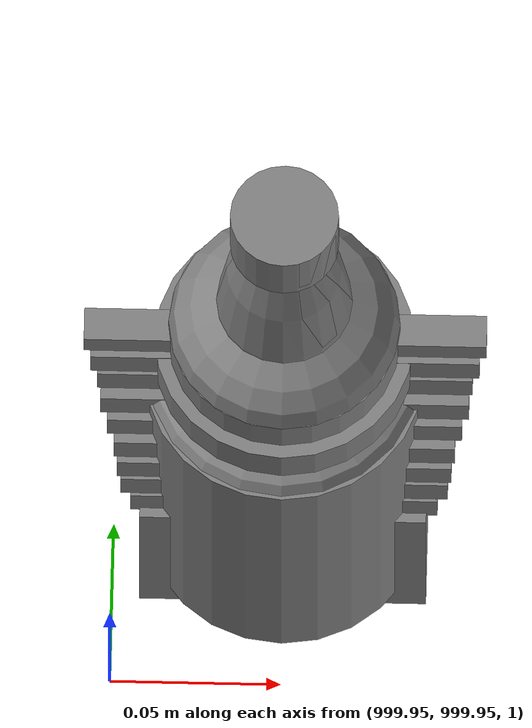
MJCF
<mujoco>
    <option gravity="0.000000000 0.000000000 -9.810000420" timestep="0.0166666" integrator="implicitfast" density="1.225" viscosity="1.8000001e-05" noslip_iterations="10" iterations="100" sdf_iterations="50">
        <flag multiccd="disable"/>
    </option>
    <size memory="1000M"/>
    <compiler coordinate="local"/>
    <worldbody>
        <light cutoff="30" pos="0 1 1" dir="0 -1 -2"/>
        <light cutoff="30" pos="0 -1 1" dir="0 1 -2"/>
        <body pos="0.000000000 0.000000000 0.000000000" euler="0.000000000 0.000000000 0.000000000" name=" Static Objects_ Static Objects">
            <geom contype="1" conaffinity="1" density="1000" type="box" material="" rgba="0.500000000 0.500000000 0.500000000 1.000000000" solimp="0.899999976 0.949999988 0.001000000" friction="1.000000000 0.005000000 0.000100000" solref="0.020000000 1.000000000" margin="0" condim="3" group="0" pos="-3.101639986 6.150595188 1.018643856" quat="1.000000000 0.000000000 0.000000000 0.000000000" size="0.050000001 0.579999983 1.019999981" name=" Static Objects_geom_A67CD707_CFC3_44E7_91D2_F239A6B680AE"/>
            <geom contype="1" conaffinity="1" density="1000" type="box" material="" rgba="0.500000000 0.500000000 0.500000000 1.000000000" solimp="0.899999976 0.949999988 0.001000000" friction="1.000000000 0.005000000 0.000100000" solref="0.020000000 1.000000000" margin="0" condim="3" group="0" pos="-2.825197220 6.153595448 1.115278244" quat="0.707107067 0.000000000 0.000000000 0.707106471" size="0.550000012 0.239999995 0.025000000" name=" Static Objects_geom_033B1560_19AF_4289_ABDE_F2458DB879B7"/>
            <geom contype="1" conaffinity="1" density="1000" type="box" material="" rgba="0.500000000 0.500000000 0.500000000 1.000000000" solimp="0.899999976 0.949999988 0.001000000" friction="1.000000000 0.005000000 0.000100000" solref="0.020000000 1.000000000" margin="0" condim="3" group="0" pos="-2.825197220 6.153595448 0.097434282" quat="0.707107067 0.000000000 0.000000000 0.707106471" size="0.550000012 0.239999995 0.098999999" name=" Static Objects_geom_3AA70981_6993_456B_9285_EE13875C0FB9"/>
            <geom contype="1" conaffinity="1" density="1000" type="box" material="" rgba="0.500000000 0.500000000 0.500000000 1.000000000" solimp="0.899999976 0.949999988 0.001000000" friction="1.000000000 0.005000000 0.000100000" solref="0.020000000 1.000000000" margin="0" condim="3" group="0" pos="-6.293097973 6.153595448 1.114443064" quat="0.707107067 0.000000000 0.000000000 0.707106471" size="0.529999971 3.134999990 0.025000000" name=" Static Objects_geom_0CB9CD4E_9B09_4296_84A8_66A64B5EEA95"/>
            <geom contype="1" conaffinity="1" density="1000" type="box" material="" rgba="0.500000000 0.500000000 0.500000000 1.000000000" solimp="0.899999976 0.949999988 0.001000000" friction="1.000000000 0.005000000 0.000100000" solref="0.020000000 1.000000000" margin="0" condim="3" group="0" pos="-2.825197220 6.153595448 1.563861728" quat="0.707107067 0.000000000 0.000000000 0.707106471" size="0.550000012 0.239999995 0.025000000" name=" Static Objects_geom_48BCE757_3961_4677_A185_069C0DA61F5C"/>
            <geom contype="1" conaffinity="1" density="1000" type="box" material="" rgba="0.500000000 0.500000000 0.500000000 1.000000000" solimp="0.899999976 0.949999988 0.001000000" friction="1.000000000 0.005000000 0.000100000" solref="0.020000000 1.000000000" margin="0" condim="3" group="0" pos="-6.311686516 6.153595448 1.018643856" quat="0.707107067 0.000000000 0.000000000 0.707106471" size="0.050000001 3.150000095 1.019999981" name=" Static Objects_geom_3B6C0E96_8C21_4841_A949_3E912F4BACBF"/>
            <geom contype="1" conaffinity="1" density="1000" type="box" material="" rgba="0.500000000 0.500000000 0.500000000 1.000000000" solimp="0.899999976 0.949999988 0.001000000" friction="1.000000000 0.005000000 0.000100000" solref="0.020000000 1.000000000" margin="0" condim="3" group="0" pos="-6.286010742 6.153595448 0.096129179" quat="0.707107067 0.000000000 0.000000000 0.707106471" size="0.529999971 3.134999990 0.098999999" name=" Static Objects_geom_EB8BAA6E_EB1A_4C52_9879_72927775200D"/>
            <geom contype="1" conaffinity="1" density="1000" type="box" material="" rgba="0.500000000 0.500000000 0.500000000 1.000000000" solimp="0.899999976 0.949999988 0.001000000" friction="1.000000000 0.005000000 0.000100000" solref="0.020000000 1.000000000" margin="0" condim="3" group="0" pos="-2.825197220 6.153595448 0.629031777" quat="0.707107067 0.000000000 0.000000000 0.707106471" size="0.550000012 0.239999995 0.025000000" name=" Static Objects_geom_C5A99976_FA6B_4E0C_899F_D40A1F68C6C9"/>
            <geom contype="1" conaffinity="1" density="1000" type="box" material="" rgba="0.500000000 0.500000000 0.500000000 1.000000000" solimp="0.899999976 0.949999988 0.001000000" friction="1.000000000 0.005000000 0.000100000" solref="0.020000000 1.000000000" margin="0" condim="3" group="0" pos="-6.286010742 6.153595448 1.563861728" quat="0.707107067 0.000000000 0.000000000 0.707106471" size="0.529999971 3.134999990 0.025000000" name=" Static Objects_geom_087FFC7D_3073_411D_AFAF_B90E331C6270"/>
            <geom contype="1" conaffinity="1" density="1000" type="box" material="" rgba="0.500000000 0.500000000 0.500000000 1.000000000" solimp="0.899999976 0.949999988 0.001000000" friction="1.000000000 0.005000000 0.000100000" solref="0.020000000 1.000000000" margin="0" condim="3" group="0" pos="-6.286010742 6.153595448 0.629031777" quat="0.707107067 0.000000000 0.000000000 0.707106471" size="0.529999971 3.134999990 0.025000000" name=" Static Objects_geom_1C7C9D85_4C88_43C0_A1BF_FCBFFB806AF9"/>
            <geom contype="1" conaffinity="1" density="1000" type="box" material="" rgba="0.500000000 0.500000000 0.500000000 1.000000000" solimp="0.899999976 0.949999988 0.001000000" friction="1.000000000 0.005000000 0.000100000" solref="0.020000000 1.000000000" margin="0" condim="3" group="0" pos="-7.719123363 2.867671013 1.173410416" quat="1.000000000 0.000000000 0.000000000 0.000000000" size="0.250000000 0.250000000 0.079999998" name=" Static Objects_geom_37CA8409_D2AE_426C_8AC6_B5DCCB3BA30B"/>
            <geom contype="1" conaffinity="1" density="1000" type="box" material="" rgba="0.500000000 0.500000000 0.500000000 1.000000000" solimp="0.899999976 0.949999988 0.001000000" friction="1.000000000 0.005000000 0.000100000" solref="0.020000000 1.000000000" margin="0" condim="3" group="0" pos="-7.408766270 3.088089943 1.776644945" quat="0.928051054 0.000000000 0.000000000 0.372453064" size="0.050000001 0.100000001 0.050000001" name=" Static Objects_geom_314CC00F_CB43_4E58_84BE_7128B3323E7E"/>
            <geom contype="1" conaffinity="1" density="1000" type="box" material="" rgba="0.500000000 0.500000000 0.500000000 1.000000000" solimp="0.899999976 0.949999988 0.001000000" friction="1.000000000 0.005000000 0.000100000" solref="0.020000000 1.000000000" margin="0" condim="3" group="0" pos="-7.719123363 2.958004713 1.530241251" quat="1.000000000 0.000000000 0.000000000 0.000000000" size="0.250000000 0.159999996 0.280000001" name=" Static Objects_geom_95564828_7434_410E_88A7_60E431C78DCA"/>
            <geom contype="1" conaffinity="1" density="1000" type="cylinder" material="" rgba="0.500000000 0.500000000 0.500000000 1.000000000" solimp="0.899999976 0.949999988 0.001000000" friction="1.000000000 0.005000000 0.000100000" solref="0.020000000 1.000000000" margin="0" condim="3" group="0" pos="-7.427312374 3.069516420 1.502544641" quat="0.928051054 0.000000000 0.000000000 0.372453064" size="0.015000000 0.230000004 0.100000001" name=" Static Objects_geom_EBBF7C1F_5F2A_461C_8239_A4C0787A7D09"/>
            <geom contype="1" conaffinity="1" density="1000" type="box" material="" rgba="0.500000000 0.500000000 0.500000000 1.000000000" solimp="0.899999976 0.949999988 0.001000000" friction="1.000000000 0.005000000 0.000100000" solref="0.020000000 1.000000000" margin="0" condim="3" group="0" pos="-7.437745571 3.067511320 1.289965630" quat="1.000000000 0.000000000 0.000000000 0.000000000" size="0.029999999 0.020000000 0.020000000" name=" Static Objects_geom_CFEABD7D_4961_4EDE_854A_0D25C6746868"/>
            <geom contype="1" conaffinity="1" density="1000" type="box" material="" rgba="0.500000000 0.500000000 0.500000000 1.000000000" solimp="0.899999976 0.949999988 0.001000000" friction="1.000000000 0.005000000 0.000100000" solref="0.020000000 1.000000000" margin="0" condim="3" group="0" pos="-9.058088303 6.434794426 1.209077358" quat="1.000000000 0.000000000 0.000000000 0.000000000" size="0.250000000 0.100000001 0.070000000" name=" Static Objects_geom_40AF58A3_9E47_4ED2_AE3B_AF162098002E"/>
            <geom contype="1" conaffinity="1" density="1000" type="box" material="" rgba="0.500000000 0.500000000 0.500000000 1.000000000" solimp="0.899999976 0.949999988 0.001000000" friction="1.000000000 0.005000000 0.000100000" solref="0.020000000 1.000000000" margin="0" condim="3" group="0" pos="-7.886891365 6.459744930 0.352518857" quat="1.000000000 0.000000000 0.000000000 0.000000000" size="1.500000000 0.200000003 0.150000006" name=" Static Objects_geom_BD496401_8C39_4EAA_98CD_2B2D419545BE"/>
            <geom contype="1" conaffinity="1" density="1000" type="box" material="" rgba="0.500000000 0.500000000 0.500000000 1.000000000" solimp="0.899999976 0.949999988 0.001000000" friction="1.000000000 0.005000000 0.000100000" solref="0.020000000 1.000000000" margin="0" condim="3" group="0" pos="-9.237723351 6.464855671 1.209077358" quat="1.000000000 0.000000000 0.000000000 0.000000000" size="0.100000001 0.100000001 0.070000000" name=" Static Objects_geom_E3E95D27_A92A_4C61_ADD9_173DFC2CB432"/>
            <geom contype="1" conaffinity="1" density="1000" type="box" material="" rgba="0.500000000 0.500000000 0.500000000 1.000000000" solimp="0.899999976 0.949999988 0.001000000" friction="1.000000000 0.005000000 0.000100000" solref="0.020000000 1.000000000" margin="0" condim="3" group="0" pos="-6.924745083 6.362090111 1.214329123" quat="1.000000000 0.000000000 0.000000000 0.000000000" size="0.200000003 0.100000001 0.075000003" name=" Static Objects_geom_C99DC3E4_8AFE_4D7E_9C26_029EF59A5225"/>
            <geom contype="1" conaffinity="1" density="1000" type="box" material="" rgba="0.500000000 0.500000000 0.500000000 1.000000000" solimp="0.899999976 0.949999988 0.001000000" friction="1.000000000 0.005000000 0.000100000" solref="0.020000000 1.000000000" margin="0" condim="3" group="0" pos="-4.407354832 6.459744930 1.292199373" quat="1.000000000 0.000000000 0.000000000 0.000000000" size="1.240000010 0.200000003 0.150000006" name=" Static Objects_geom_14E72071_1E10_4DDB_8EC9_9B22037A885E"/>
            <geom contype="1" conaffinity="1" density="1000" type="box" material="" rgba="0.500000000 0.500000000 0.500000000 1.000000000" solimp="0.899999976 0.949999988 0.001000000" friction="1.000000000 0.005000000 0.000100000" solref="0.020000000 1.000000000" margin="0" condim="3" group="0" pos="-5.611940861 6.318420410 0.350975692" quat="1.000000000 0.000000000 0.000000000 0.000000000" size="0.699999988 0.100000001 0.150000006" name=" Static Objects_geom_641E2199_11F6_470F_884A_5AC1E69DB1BE"/>
            <geom contype="1" conaffinity="1" density="1000" type="box" material="" rgba="0.500000000 0.500000000 0.500000000 1.000000000" solimp="0.899999976 0.949999988 0.001000000" friction="1.000000000 0.005000000 0.000100000" solref="0.020000000 1.000000000" margin="0" condim="3" group="0" pos="-6.300771236 6.459744930 1.744376063" quat="1.000000000 0.000000000 0.000000000 0.000000000" size="3.000000000 0.200000003 0.150000006" name=" Static Objects_geom_42DAC77A_0444_4DFE_8592_4FAD22CEE0D2"/>
            <geom contype="1" conaffinity="1" density="1000" type="box" material="" rgba="0.500000000 0.500000000 0.500000000 1.000000000" solimp="0.899999976 0.949999988 0.001000000" friction="1.000000000 0.005000000 0.000100000" solref="0.020000000 1.000000000" margin="0" condim="3" group="0" pos="-8.844120979 6.464855671 1.209077358" quat="1.000000000 0.000000000 0.000000000 0.000000000" size="0.100000001 0.100000001 0.070000000" name=" Static Objects_geom_B34304A4_9660_4DF0_AD48_2F1158963659"/>
            <geom contype="1" conaffinity="1" density="1000" type="box" material="" rgba="0.500000000 0.500000000 0.500000000 1.000000000" solimp="0.899999976 0.949999988 0.001000000" friction="1.000000000 0.005000000 0.000100000" solref="0.020000000 1.000000000" margin="0" condim="3" group="0" pos="-6.824534416 6.447464466 1.212718010" quat="1.000000000 0.000000000 0.000000000 0.000000000" size="0.100000001 0.100000001 0.075000003" name=" Static Objects_geom_A9D4AFC7_09E2_4B64_9A5E_5754634F2793"/>
            <geom contype="1" conaffinity="1" density="1000" type="box" material="" rgba="0.500000000 0.500000000 0.500000000 1.000000000" solimp="0.899999976 0.949999988 0.001000000" friction="1.000000000 0.005000000 0.000100000" solref="0.020000000 1.000000000" margin="0" condim="3" group="0" pos="-6.751636982 6.459744930 0.800981164" quat="1.000000000 0.000000000 0.000000000 0.000000000" size="2.200000048 0.200000003 0.150000006" name=" Static Objects_geom_6876503E_9E95_477C_BBFB_1524212DE8DD"/>
            <geom contype="1" conaffinity="1" density="1000" type="box" material="" rgba="0.500000000 0.500000000 0.500000000 1.000000000" solimp="0.899999976 0.949999988 0.001000000" friction="1.000000000 0.005000000 0.000100000" solref="0.020000000 1.000000000" margin="0" condim="3" group="0" pos="-6.098561764 6.327973843 1.292199373" quat="1.000000000 0.000000000 0.000000000 0.000000000" size="0.500000000 0.100000001 0.150000006" name=" Static Objects_geom_6645E8D9_C0FA_49EB_8DC4_A07BBA2121A1"/>
            <geom contype="1" conaffinity="1" density="1000" type="box" material="" rgba="0.500000000 0.500000000 0.500000000 1.000000000" solimp="0.899999976 0.949999988 0.001000000" friction="1.000000000 0.005000000 0.000100000" solref="0.020000000 1.000000000" margin="0" condim="3" group="0" pos="-3.907610416 6.318625927 0.800981164" quat="1.000000000 0.000000000 0.000000000 0.000000000" size="0.500000000 0.100000001 0.150000006" name=" Static Objects_geom_B30F8060_B80D_4F92_8858_A7EC6D7D96C1"/>
            <geom contype="1" conaffinity="1" density="1000" type="box" material="" rgba="0.500000000 0.500000000 0.500000000 1.000000000" solimp="0.899999976 0.949999988 0.001000000" friction="1.000000000 0.005000000 0.000100000" solref="0.020000000 1.000000000" margin="0" condim="3" group="0" pos="-7.373087406 6.458900928 1.214329123" quat="1.000000000 0.000000000 0.000000000 0.000000000" size="0.250000000 0.200000003 0.075000003" name=" Static Objects_geom_5E9C1F75_A91D_4607_988C_B106EEBE06F9"/>
            <geom contype="1" conaffinity="1" density="1000" type="box" material="" rgba="0.500000000 0.500000000 0.500000000 1.000000000" solimp="0.899999976 0.949999988 0.001000000" friction="1.000000000 0.005000000 0.000100000" solref="0.020000000 1.000000000" margin="0" condim="3" group="0" pos="-4.035642624 6.459744930 0.352518857" quat="1.000000000 0.000000000 0.000000000 0.000000000" size="0.800000012 0.200000003 0.150000006" name=" Static Objects_geom_226109F2_4B61_4AC4_95BA_6FCBF556249D"/>
            <geom contype="1" conaffinity="1" density="1000" type="box" material="" rgba="0.500000000 0.500000000 0.500000000 1.000000000" solimp="0.899999976 0.949999988 0.001000000" friction="1.000000000 0.005000000 0.000100000" solref="0.020000000 1.000000000" margin="0" condim="3" group="0" pos="-6.460197449 2.937205315 0.548931718" quat="1.000000000 0.000000000 0.000000000 0.000000000" size="2.650000095 0.430000007 0.550000012" name=" Static Objects_geom_1BD292B1_C11D_457D_95C3_D8B854F699A4"/>
            <geom contype="1" conaffinity="1" density="1000" type="box" material="" rgba="0.500000000 0.500000000 0.500000000 1.000000000" solimp="0.899999976 0.949999988 0.001000000" friction="1.000000000 0.005000000 0.000100000" solref="0.020000000 1.000000000" margin="0" condim="3" group="0" pos="-4.240264893 1.327049494 0.549888909" quat="1.000000000 0.000000000 0.000000000 0.000000000" size="0.430000007 1.200000048 0.550000012" name=" Static Objects_geom_58B13528_52D1_470D_B44B_6231B042A461"/>
            <geom contype="1" conaffinity="1" density="1000" type="box" material="" rgba="0.500000000 0.500000000 0.500000000 1.000000000" solimp="0.899999976 0.949999988 0.001000000" friction="1.000000000 0.005000000 0.000100000" solref="0.020000000 1.000000000" margin="0" condim="3" group="0" pos="-8.830721855 2.096410990 0.549305558" quat="1.000000000 0.000000000 0.000000000 0.000000000" size="0.280000001 0.430000007 0.550000012" name=" Static Objects_geom_56AC7991_F821_4A5C_B90C_87546087DD89"/>
            <geom contype="1" conaffinity="1" density="1000" type="plane" material="" rgba="0.500000000 0.500000000 0.500000000 1.000000000" solimp="0.899999976 0.949999988 0.001000000" friction="1.000000000 0.005000000 0.000100000" solref="0.020000000 1.000000000" margin="0" condim="3" group="0" pos="-6.000000000 10.399999619 0.000000000" quat="1.000000000 0.000000000 0.000000000 0.000000000" size="6.050000191 10.800000191 0.010000000" name=" Static Objects_geom_8E3BC73C_12C2_4D8B_AC1C_ED187C48B858"/>
            <geom contype="1" conaffinity="1" density="1000" type="box" material="" rgba="0.500000000 0.500000000 0.500000000 1.000000000" solimp="0.899999976 0.949999988 0.001000000" friction="1.000000000 0.005000000 0.000100000" solref="0.020000000 1.000000000" margin="0" condim="3" group="0" pos="-6.000000000 0.035000000 2.000000000" quat="1.000000000 0.000000000 0.000000000 0.000000000" size="6.079999924 0.070000000 2.000000000" name=" Static Objects_geom_D1B847E7_DF0F_4357_9A6F_D7D661B537BE"/>
            <geom contype="1" conaffinity="1" density="1000" type="box" material="" rgba="0.500000000 0.500000000 0.500000000 1.000000000" solimp="0.899999976 0.949999988 0.001000000" friction="1.000000000 0.005000000 0.000100000" solref="0.020000000 1.000000000" margin="0" condim="3" group="0" pos="-6.000000000 20.159999847 2.000000000" quat="1.000000000 0.000000000 0.000000000 0.000000000" size="6.079999924 0.070000000 2.000000000" name=" Static Objects_geom_D943A244_BAC9_47FC_A534_C46DF4325DAE"/>
            <geom contype="1" conaffinity="1" density="1000" type="box" material="" rgba="0.500000000 0.500000000 0.500000000 1.000000000" solimp="0.899999976 0.949999988 0.001000000" friction="1.000000000 0.005000000 0.000100000" solref="0.020000000 1.000000000" margin="0" condim="3" group="0" pos="0.000000000 10.000000000 2.000000000" quat="1.000000000 0.000000000 0.000000000 0.000000000" size="0.070000000 10.500000000 2.000000000" name=" Static Objects_geom_6964FB2D_9442_45D0_A769_6B49992992D8"/>
            <geom contype="1" conaffinity="1" density="1000" type="box" material="" rgba="0.500000000 0.500000000 0.500000000 1.000000000" solimp="0.899999976 0.949999988 0.001000000" friction="1.000000000 0.005000000 0.000100000" solref="0.020000000 1.000000000" margin="0" condim="3" group="0" pos="-12.050000191 10.000000000 2.000000000" quat="1.000000000 0.000000000 0.000000000 0.000000000" size="0.070000000 10.500000000 2.000000000" name=" Static Objects_geom_9C491FE6_7AED_4993_9044_BB1EDEC98E87"/>
        </body>
        <body pos="-2.315349817 5.979455948 1.771015525" euler="-39.274703979 -68.425415039 91.379066467" mocap="true" name="spotlight4_SpotLight"/>
        <body pos="-2.217953444 6.148818493 1.678929090" euler="-120.588432312 -7.943731785 -175.305343628" mocap="true" name="spotlight5_SpotLight"/>
        <body pos="1000.000000000 1000.000000000 1.000000000" euler="0.000000000 0.000000000 0.000000000" name="openloong_gripper_2f85_fix_base_usda_jar_01">
            <geom contype="1" conaffinity="1" density="1000" type="box" material="" rgba="0.500000000 0.500000000 0.500000000 1.000000000" solimp="0.899999976 0.949999988 0.001000000" friction="1.000000000 0.005000000 0.000100000" solref="0.020000000 1.000000000" margin="0" condim="3" group="0" pos="0.000000000 0.000000000 0.006158113" quat="1.000000000 0.000000000 0.000000000 0.000000000" size="0.020000000 0.020000000 0.005000000" name="openloong_gripper_2f85_fix_base_usda_geom_E8ECEC29_5365_49D2_BBEB_BEA226AD6D68"/>
            <geom contype="1" conaffinity="1" density="1000" type="cylinder" material="" rgba="0.500000000 0.500000000 0.500000000 1.000000000" solimp="0.899999976 0.949999988 0.001000000" friction="1.000000000 0.005000000 0.000100000" solref="0.020000000 1.000000000" margin="0" condim="3" group="0" pos="0.000000000 0.000000000 0.062744498" quat="1.000000000 0.000000000 0.000000000 0.000000000" size="0.041000001 0.052999999 1.000000000" name="openloong_gripper_2f85_fix_base_usda_geom_FBB4AA47_0A26_4F6C_828F_2F0B6A164262"/>
            <geom contype="1" conaffinity="1" density="1000" type="ellipsoid" material="" rgba="0.500000000 0.500000000 0.500000000 1.000000000" solimp="0.899999976 0.949999988 0.001000000" friction="1.000000000 0.005000000 0.000100000" solref="0.020000000 1.000000000" margin="0" condim="3" group="0" pos="0.000000000 0.000000000 0.122252703" quat="1.000000000 0.000000000 0.000000000 0.000000000" size="0.035999998 0.035999998 0.010000000" name="openloong_gripper_2f85_fix_base_usda_geom_B5E16AF9_B5CE_420A_B927_DFBEB61CE49A"/>
            <geom contype="1" conaffinity="1" density="1000" type="cylinder" material="" rgba="0.500000000 0.500000000 0.500000000 1.000000000" solimp="0.899999976 0.949999988 0.001000000" friction="1.000000000 0.005000000 0.000100000" solref="0.020000000 1.000000000" margin="0" condim="3" group="0" pos="0.000000000 0.000000000 0.015747190" quat="1.000000000 0.000000000 0.000000000 0.000000000" size="0.035000000 0.010000000 1.000000000" name="openloong_gripper_2f85_fix_base_usda_geom_5FEDC9A3_6120_4711_BA63_5D5CC63DBEED"/>
            <geom contype="1" conaffinity="1" density="1000" type="ellipsoid" material="" rgba="0.500000000 0.500000000 0.500000000 1.000000000" solimp="0.899999976 0.949999988 0.001000000" friction="1.000000000 0.005000000 0.000100000" solref="0.020000000 1.000000000" margin="0" condim="3" group="0" pos="0.000000000 0.000000000 0.115815401" quat="1.000000000 0.000000000 0.000000000 0.000000000" size="0.039999999 0.039999999 0.010000000" name="openloong_gripper_2f85_fix_base_usda_geom_6E68540A_F36D_4B0F_8C54_EB048BD76FF7"/>
            <geom contype="1" conaffinity="1" density="1000" type="cylinder" material="" rgba="0.500000000 0.500000000 0.500000000 1.000000000" solimp="0.899999976 0.949999988 0.001000000" friction="1.000000000 0.005000000 0.000100000" solref="0.020000000 1.000000000" margin="0" condim="3" group="0" pos="0.000000000 0.000000000 0.133183479" quat="1.000000000 0.000000000 0.000000000 0.000000000" size="0.037999999 0.006500000 1.000000000" name="openloong_gripper_2f85_fix_base_usda_geom_F94AEFAB_A64E_47E9_9FAA_1A458C49D5DA"/>
            <freejoint name="openloong_gripper_2f85_fix_base_usda_jar_01_joint"/>
            <site size="0.005000000 0.005000000 0.005000000" rgba="0.500000000 0.500000000 0.500000000 1.000000000" pos="0.000000000 0.000000000 0.000000000" quat="1.000000000 0.000000000 0.000000000 0.000000000" group="0" type="sphere" name="openloong_gripper_2f85_fix_base_usda_jar_01site"/>
        </body>
        <body pos="1000.000000000 1000.000000000 1.000000000" euler="0.000000000 0.000000000 0.000000000" name="openloong_gripper_2f85_fix_base_usda_bottle_blue">
            <geom contype="1" conaffinity="1" density="1000" type="ellipsoid" material="" rgba="0.500000000 0.500000000 0.500000000 1.000000000" solimp="0.899999976 0.949999988 0.001000000" friction="1.000000000 0.005000000 0.000100000" solref="0.020000000 1.000000000" margin="0" condim="3" group="0" pos="0.000000000 0.000000000 0.118920922" quat="1.000000000 0.000000000 0.000000000 0.000000000" size="0.030999999 0.030999999 0.029999999" name="openloong_gripper_2f85_fix_base_usda_geom_F073B49F_9A56_4D52_9CEA_3DF0BD5C93F5"/>
            <geom contype="1" conaffinity="1" density="1000" type="box" material="" rgba="0.500000000 0.500000000 0.500000000 1.000000000" solimp="0.899999976 0.949999988 0.001000000" friction="1.000000000 0.005000000 0.000100000" solref="0.020000000 1.000000000" margin="0" condim="3" group="0" pos="0.000000000 0.000000000 0.002164602" quat="1.000000000 0.000000000 0.000000000 0.000000000" size="0.020000000 0.020000000 0.003000000" name="openloong_gripper_2f85_fix_base_usda_geom_09F01916_9F30_4DF3_8066_B398B708C009"/>
            <geom contype="1" conaffinity="1" density="1000" type="cylinder" material="" rgba="0.500000000 0.500000000 0.500000000 1.000000000" solimp="0.899999976 0.949999988 0.001000000" friction="1.000000000 0.005000000 0.000100000" solref="0.020000000 1.000000000" margin="0" condim="3" group="0" pos="0.000000000 -0.000366211 0.060859680" quat="1.000000000 0.000000000 0.000000000 0.000000000" size="0.030999999 0.057999998 1.000000000" name="openloong_gripper_2f85_fix_base_usda_geom_D3276512_12B3_4302_BB11_496E45AED997"/>
            <geom contype="1" conaffinity="1" density="1000" type="cylinder" material="" rgba="0.500000000 0.500000000 0.500000000 1.000000000" solimp="0.899999976 0.949999988 0.001000000" friction="1.000000000 0.005000000 0.000100000" solref="0.020000000 1.000000000" margin="0" condim="3" group="0" pos="0.000000000 0.000000000 0.220594406" quat="1.000000000 0.000000000 0.000000000 0.000000000" size="0.016000001 0.010000000 1.000000000" name="openloong_gripper_2f85_fix_base_usda_geom_D4FC8FB2_8DD4_4D24_818B_BB6E31E1B282"/>
            <geom contype="1" conaffinity="1" density="1000" type="ellipsoid" material="" rgba="0.500000000 0.500000000 0.500000000 1.000000000" solimp="0.899999976 0.949999988 0.001000000" friction="1.000000000 0.005000000 0.000100000" solref="0.020000000 1.000000000" margin="0" condim="3" group="0" pos="0.000000000 0.000000000 0.144259930" quat="1.000000000 0.000000000 0.000000000 0.000000000" size="0.021000000 0.021000000 0.079999998" name="openloong_gripper_2f85_fix_base_usda_geom_E7728D13_94F8_4BE8_BFB1_133A51A8460A"/>
            <freejoint name="openloong_gripper_2f85_fix_base_usda_bottle_blue_joint"/>
            <site size="0.005000000 0.005000000 0.005000000" rgba="0.500000000 0.500000000 0.500000000 1.000000000" pos="0.000000000 0.000000000 0.000000000" quat="0.999961913 0.008726535 0.000000000 0.000000000" group="0" type="sphere" name="openloong_gripper_2f85_fix_base_usda_bottle_bluesite"/>
        </body>
        <body pos="-2.062295437 6.387450218 1.752344131" euler="-102.356346130 -1.989956498 -0.057625629" mocap="true" name="spotlight1_SpotLight"/>
        <body pos="1000.000000000 1000.000000000 1.000000000" euler="0.000000000 0.000000000 0.000000000" name="openloong_gripper_2f85_fix_base_usda_salt">
            <geom contype="1" conaffinity="1" density="1000" type="box" material="" rgba="0.500000000 0.500000000 0.500000000 1.000000000" solimp="0.899999976 0.949999988 0.001000000" friction="1.000000000 0.005000000 0.000100000" solref="0.020000000 1.000000000" margin="0" condim="3" group="0" pos="0.000305176 0.000000000 0.084862232" quat="1.000000000 0.000000000 0.000000000 0.000000000" size="0.048999999 0.018999999 0.005000000" name="openloong_gripper_2f85_fix_base_usda_geom_394619DF_A05B_44A8_AEFF_774AEA333B85"/>
            <geom contype="1" conaffinity="1" density="1000" type="box" material="" rgba="0.500000000 0.500000000 0.500000000 1.000000000" solimp="0.899999976 0.949999988 0.001000000" friction="1.000000000 0.005000000 0.000100000" solref="0.020000000 1.000000000" margin="0" condim="3" group="0" pos="0.000305176 0.000000000 0.104564309" quat="1.000000000 0.000000000 0.000000000 0.000000000" size="0.052000001 0.014000000 0.005000000" name="openloong_gripper_2f85_fix_base_usda_geom_97C20E8D_E353_4AD4_BC5B_7039C1CD55EF"/>
            <geom contype="1" conaffinity="1" density="1000" type="box" material="" rgba="0.500000000 0.500000000 0.500000000 1.000000000" solimp="0.899999976 0.949999988 0.001000000" friction="1.000000000 0.005000000 0.000100000" solref="0.020000000 1.000000000" margin="0" condim="3" group="0" pos="0.000305176 0.000000000 0.114487171" quat="1.000000000 0.000000000 0.000000000 0.000000000" size="0.054000001 0.011500000 0.005000000" name="openloong_gripper_2f85_fix_base_usda_geom_3F83B8C8_F88A_4A56_9AFF_B745A661559B"/>
            <geom contype="1" conaffinity="1" density="1000" type="box" material="" rgba="0.500000000 0.500000000 0.500000000 1.000000000" solimp="0.899999976 0.949999988 0.001000000" friction="1.000000000 0.005000000 0.000100000" solref="0.020000000 1.000000000" margin="0" condim="3" group="0" pos="0.000305176 0.000000000 0.075103164" quat="1.000000000 0.000000000 0.000000000 0.000000000" size="0.048000000 0.020000000 0.005000000" name="openloong_gripper_2f85_fix_base_usda_geom_E1F45154_C6CF_4B1F_A993_303FE9D08557"/>
            <geom contype="1" conaffinity="1" density="1000" type="box" material="" rgba="0.500000000 0.500000000 0.500000000 1.000000000" solimp="0.899999976 0.949999988 0.001000000" friction="1.000000000 0.005000000 0.000100000" solref="0.020000000 1.000000000" margin="0" condim="3" group="0" pos="0.000305176 0.000000000 0.134892464" quat="1.000000000 0.000000000 0.000000000 0.000000000" size="0.057000000 0.007000000 0.005000000" name="openloong_gripper_2f85_fix_base_usda_geom_0E178317_88B7_4EB1_B558_2F809C0F9A74"/>
            <geom contype="1" conaffinity="1" density="1000" type="box" material="" rgba="0.500000000 0.500000000 0.500000000 1.000000000" solimp="0.899999976 0.949999988 0.001000000" friction="1.000000000 0.005000000 0.000100000" solref="0.020000000 1.000000000" margin="0" condim="3" group="0" pos="0.000305176 0.000000000 0.094920278" quat="1.000000000 0.000000000 0.000000000 0.000000000" size="0.050000001 0.017000001 0.005000000" name="openloong_gripper_2f85_fix_base_usda_geom_5E0700D3_9AE2_49F7_929C_FDBFBF969442"/>
            <geom contype="1" conaffinity="1" density="1000" type="box" material="" rgba="0.500000000 0.500000000 0.500000000 1.000000000" solimp="0.899999976 0.949999988 0.001000000" friction="1.000000000 0.005000000 0.000100000" solref="0.020000000 1.000000000" margin="0" condim="3" group="0" pos="0.000305176 0.000000000 0.065204859" quat="1.000000000 0.000000000 0.000000000 0.000000000" size="0.045000002 0.021000000 0.005000000" name="openloong_gripper_2f85_fix_base_usda_geom_71955DCD_73D6_4F2D_BFAE_66443492A0FB"/>
            <geom contype="1" conaffinity="1" density="1000" type="box" material="" rgba="0.500000000 0.500000000 0.500000000 1.000000000" solimp="0.899999976 0.949999988 0.001000000" friction="1.000000000 0.005000000 0.000100000" solref="0.020000000 1.000000000" margin="0" condim="3" group="0" pos="0.000305176 0.000000000 0.144135714" quat="1.000000000 0.000000000 0.000000000 0.000000000" size="0.059000000 0.005000000 0.004000000" name="openloong_gripper_2f85_fix_base_usda_geom_64DEB293_592A_4E70_B4A7_DDD7B7B7A1D6"/>
            <geom contype="1" conaffinity="1" density="1000" type="box" material="" rgba="0.500000000 0.500000000 0.500000000 1.000000000" solimp="0.899999976 0.949999988 0.001000000" friction="1.000000000 0.005000000 0.000100000" solref="0.020000000 1.000000000" margin="0" condim="3" group="0" pos="0.000000000 0.000000000 0.031593561" quat="1.000000000 0.000000000 0.000000000 0.000000000" size="0.041999999 0.024000000 0.029999999" name="openloong_gripper_2f85_fix_base_usda_geom_E98D8C67_ABAB_4E81_B547_0A4A4D3D096A"/>
            <geom contype="1" conaffinity="1" density="1000" type="box" material="" rgba="0.500000000 0.500000000 0.500000000 1.000000000" solimp="0.899999976 0.949999988 0.001000000" friction="1.000000000 0.005000000 0.000100000" solref="0.020000000 1.000000000" margin="0" condim="3" group="0" pos="0.000305176 0.000000000 0.124608755" quat="1.000000000 0.000000000 0.000000000 0.000000000" size="0.055000000 0.008000000 0.005000000" name="openloong_gripper_2f85_fix_base_usda_geom_BE123CF5_6C72_4C73_AAC4_12A09984BB81"/>
            <freejoint name="openloong_gripper_2f85_fix_base_usda_salt_joint"/>
            <site size="0.005000000 0.005000000 0.005000000" rgba="0.500000000 0.500000000 0.500000000 1.000000000" pos="0.000000000 0.000000000 0.000000000" quat="1.000000000 0.000000000 0.000000000 0.000000000" group="0" type="sphere" name="openloong_gripper_2f85_fix_base_usda_saltsite"/>
        </body>
        <body pos="1000.000000000 1000.000000000 1.000000000" euler="0.000000000 0.000000000 0.000000000" name="openloong_gripper_2f85_fix_base_usda_can">
            <geom contype="1" conaffinity="1" density="1000" type="cylinder" material="" rgba="0.500000000 0.500000000 0.500000000 1.000000000" solimp="0.899999976 0.949999988 0.001000000" friction="1.000000000 0.005000000 0.000100000" solref="0.020000000 1.000000000" margin="0" condim="3" group="0" pos="0.000000000 0.000000000 0.079676986" quat="1.000000000 0.000000000 0.000000000 0.000000000" size="0.034000002 0.071999997 1.000000000" name="openloong_gripper_2f85_fix_base_usda_geom_D79B2805_D2BD_4B51_B29E_B1C2B54299D9"/>
            <geom contype="1" conaffinity="1" density="1000" type="ellipsoid" material="" rgba="0.500000000 0.500000000 0.500000000 1.000000000" solimp="0.899999976 0.949999988 0.001000000" friction="1.000000000 0.005000000 0.000100000" solref="0.020000000 1.000000000" margin="0" condim="3" group="0" pos="0.000000000 0.000000000 0.151854277" quat="1.000000000 0.000000000 0.000000000 0.000000000" size="0.034000002 0.034000002 0.020000000" name="openloong_gripper_2f85_fix_base_usda_geom_92B00C38_A39E_4106_BAE7_F583D8FA49EE"/>
            <geom contype="1" conaffinity="1" density="1000" type="box" material="" rgba="0.500000000 0.500000000 0.500000000 1.000000000" solimp="0.899999976 0.949999988 0.001000000" friction="1.000000000 0.005000000 0.000100000" solref="0.020000000 1.000000000" margin="0" condim="3" group="0" pos="0.000000000 0.000000000 0.004777670" quat="1.000000000 0.000000000 0.000000000 0.000000000" size="0.020000000 0.020000000 0.005000000" name="openloong_gripper_2f85_fix_base_usda_geom_4D634C2B_16CA_4F68_8E45_540858EEE120"/>
            <freejoint name="openloong_gripper_2f85_fix_base_usda_can_joint"/>
            <site size="0.005000000 0.005000000 0.005000000" rgba="0.500000000 0.500000000 0.500000000 1.000000000" pos="0.000000000 0.000000000 0.000000000" quat="1.000000000 0.000000000 0.000000000 0.000000000" group="0" type="sphere" name="openloong_gripper_2f85_fix_base_usda_cansite"/>
        </body>
        <body pos="1000.000000000 1000.000000000 1.000000000" euler="0.000000000 0.000000000 0.000000000" name="openloong_gripper_2f85_fix_base_usda_bottle_red">
            <geom contype="1" conaffinity="1" density="1000" type="ellipsoid" material="" rgba="0.500000000 0.500000000 0.500000000 1.000000000" solimp="0.899999976 0.949999988 0.001000000" friction="1.000000000 0.005000000 0.000100000" solref="0.020000000 1.000000000" margin="0" condim="3" group="0" pos="0.000000000 0.000000000 0.144284487" quat="1.000000000 0.000000000 0.000000000 0.000000000" size="0.021000000 0.021000000 0.079999998" name="openloong_gripper_2f85_fix_base_usda_geom_B09129CE_E839_46BD_B617_BD1267AECDCB"/>
            <geom contype="1" conaffinity="1" density="1000" type="cylinder" material="" rgba="0.500000000 0.500000000 0.500000000 1.000000000" solimp="0.899999976 0.949999988 0.001000000" friction="1.000000000 0.005000000 0.000100000" solref="0.020000000 1.000000000" margin="0" condim="3" group="0" pos="0.000000000 0.000000000 0.220618963" quat="1.000000000 0.000000000 0.000000000 0.000000000" size="0.016000001 0.010000000 1.000000000" name="openloong_gripper_2f85_fix_base_usda_geom_2DFF3551_B88A_4826_9591_95B13BD96485"/>
            <geom contype="1" conaffinity="1" density="1000" type="ellipsoid" material="" rgba="0.500000000 0.500000000 0.500000000 1.000000000" solimp="0.899999976 0.949999988 0.001000000" friction="1.000000000 0.005000000 0.000100000" solref="0.020000000 1.000000000" margin="0" condim="3" group="0" pos="0.000000000 0.000000000 0.118945479" quat="1.000000000 0.000000000 0.000000000 0.000000000" size="0.030999999 0.030999999 0.029999999" name="openloong_gripper_2f85_fix_base_usda_geom_76F59DE1_E246_4B5F_8DDD_48FD359B2898"/>
            <geom contype="1" conaffinity="1" density="1000" type="box" material="" rgba="0.500000000 0.500000000 0.500000000 1.000000000" solimp="0.899999976 0.949999988 0.001000000" friction="1.000000000 0.005000000 0.000100000" solref="0.020000000 1.000000000" margin="0" condim="3" group="0" pos="0.000000000 0.000000000 0.002189159" quat="1.000000000 0.000000000 0.000000000 0.000000000" size="0.020000000 0.020000000 0.003000000" name="openloong_gripper_2f85_fix_base_usda_geom_A028AFC5_A007_4B1F_BDEA_98B989ACA119"/>
            <geom contype="1" conaffinity="1" density="1000" type="cylinder" material="" rgba="0.500000000 0.500000000 0.500000000 1.000000000" solimp="0.899999976 0.949999988 0.001000000" friction="1.000000000 0.005000000 0.000100000" solref="0.020000000 1.000000000" margin="0" condim="3" group="0" pos="0.000000000 -0.000366211 0.060884237" quat="1.000000000 0.000000000 0.000000000 0.000000000" size="0.030999999 0.057999998 1.000000000" name="openloong_gripper_2f85_fix_base_usda_geom_D729CF8E_EB8F_439A_8AEC_CB59FF07C5B7"/>
            <freejoint name="openloong_gripper_2f85_fix_base_usda_bottle_red_joint"/>
            <site size="0.005000000 0.005000000 0.005000000" rgba="0.500000000 0.500000000 0.500000000 1.000000000" pos="0.000000000 0.000000000 0.000000000" quat="0.999961913 0.008726535 0.000000000 0.000000000" group="0" type="sphere" name="openloong_gripper_2f85_fix_base_usda_bottle_redsite"/>
        </body>
        <body pos="0.000000000 0.000000000 0.000000000" euler="0.000000000 0.000000000 0.000000000" name="Interactive Objects_Interactive Objects"/>
        <body pos="-3.510578632 3.403555870 -0.000000100" euler="0.000000000 0.000000000 40.200675964" name="openloong_gripper_2f85_fix_base_usda_PZ">
            <geom contype="1" conaffinity="1" density="1000" type="box" material="" rgba="0.500000000 0.500000000 0.500000000 1.000000000" solimp="0.899999976 0.949999988 0.001000000" friction="1.000000000 0.005000000 0.000100000" solref="0.020000000 1.000000000" margin="0" condim="3" group="0" pos="-0.047453165 0.056484699 0.373715430" quat="0.934750080 0.077914521 0.028795123 0.345459938" size="0.180000007 0.010000000 0.379999995" name="openloong_gripper_2f85_fix_base_usda_geom_5EA74023_F4A2_4876_919B_5B189AA426CD"/>
            <geom contype="1" conaffinity="1" density="1000" type="box" material="" rgba="0.500000000 0.500000000 0.500000000 1.000000000" solimp="0.899999976 0.949999988 0.001000000" friction="1.000000000 0.005000000 0.000100000" solref="0.020000000 1.000000000" margin="0" condim="3" group="0" pos="0.047452450 -0.054376602 0.374072611" quat="0.934387863 -0.082143910 -0.030358355 0.345326364" size="0.180000007 0.010000000 0.379999995" name="openloong_gripper_2f85_fix_base_usda_geom_1B03FECC_9119_452E_BCCD_1579BC802ED5"/>
            <freejoint name="openloong_gripper_2f85_fix_base_usda_PZ"/>
        </body>
        <body pos="-6.332345009 2.779978037 1.034067392" euler="0.000000000 0.000000000 0.000000000" name="openloong_gripper_2f85_fix_base_usda_basket">
            <geom contype="1" conaffinity="1" density="100000" type="box" material="" rgba="0.500000000 0.500000000 0.500000000 1.000000000" solimp="0.899999976 0.949999988 0.001000000" friction="1.000000000 0.899999976 0.000100000" solref="0.020000000 1.000000000" margin="0" condim="3" group="0" pos="-0.172339439 0.000000000 0.168361664" quat="0.706172407 -0.036353018 -0.036353093 0.706170976" size="0.200000003 0.006000000 0.108000003" name="openloong_gripper_2f85_fix_base_usda_geom_3971FEC4_3266_4729_A34A_CA4E9B152EFA"/>
            <geom contype="1" conaffinity="1" density="100000" type="box" material="" rgba="0.500000000 0.500000000 0.500000000 1.000000000" solimp="0.899999976 0.949999988 0.001000000" friction="1.000000000 0.899999976 0.000100000" solref="0.020000000 1.000000000" margin="0" condim="3" group="0" pos="-0.039724827 -0.188568115 0.167089701" quat="0.997537494 0.070135131 0.000000000 0.000000000" size="0.150000006 0.006000000 0.108000003" name="openloong_gripper_2f85_fix_base_usda_geom_53ED8E18_2C8C_4477_96F2_13BE7BC41A56"/>
            <geom contype="1" conaffinity="1" density="100000" type="box" material="" rgba="0.500000000 0.500000000 0.500000000 1.000000000" solimp="0.899999976 0.949999988 0.001000000" friction="1.000000000 0.899999976 0.000100000" solref="0.020000000 1.000000000" margin="0" condim="3" group="0" pos="-0.039724827 0.188377380 0.167089701" quat="0.997489929 -0.070808925 0.000000000 0.000000000" size="0.150000006 0.006000000 0.108000003" name="openloong_gripper_2f85_fix_base_usda_geom_50323691_6ACE_49AE_9865_FA69F0CF8893"/>
            <geom contype="1" conaffinity="1" density="100000" type="box" material="" rgba="0.500000000 0.500000000 0.500000000 1.000000000" solimp="0.899999976 0.949999988 0.001000000" friction="1.000000000 0.899999976 0.000100000" solref="0.020000000 1.000000000" margin="0" condim="3" group="0" pos="-0.039724827 0.000000000 0.068126202" quat="1.000000000 0.000000000 0.000000000 0.000000000" size="0.129999995 0.174999997 0.006000000" name="openloong_gripper_2f85_fix_base_usda_geom_FD815EEE_0D43_4B99_B5D6_D2303984A5C7"/>
            <geom contype="1" conaffinity="1" density="100000" type="box" material="" rgba="0.500000000 0.500000000 0.500000000 1.000000000" solimp="0.899999976 0.949999988 0.001000000" friction="1.000000000 0.899999976 0.000100000" solref="0.020000000 1.000000000" margin="0" condim="3" group="0" pos="0.094372749 0.000000000 0.168361664" quat="0.706172049 0.036353335 0.036353379 0.706171215" size="0.200000003 0.006000000 0.108000003" name="openloong_gripper_2f85_fix_base_usda_geom_15FD1C8A_33B2_4E39_99C8_AD559D9531C2"/>
            <freejoint name="openloong_gripper_2f85_fix_base_usda_basket_joint"/>
            <site size="0.005000000 0.005000000 0.005000000" rgba="0.500000000 0.500000000 0.500000000 1.000000000" pos="0.000000000 0.000000000 0.000000000" quat="1.000000000 0.000000000 0.000000000 0.000000000" group="0" type="sphere" name="openloong_gripper_2f85_fix_base_usda_basketsite"/>
        </body>
        <body pos="-7.168000221 2.823999882 1.227496982" euler="-0.283413976 0.056829724 -0.133293271" name="openloong_gripper_2f85_fix_base_usda_Pos">
            <geom contype="1" conaffinity="1" density="1000" type="box" material="" rgba="0.500000000 0.500000000 0.500000000 1.000000000" solimp="0.899999976 0.949999988 0.001000000" friction="1.000000000 0.005000000 0.000100000" solref="0.020000000 1.000000000" margin="0" condim="3" group="0" pos="-0.002278805 0.074524641 -0.004134059" quat="0.315989345 0.948763072 -0.000000000 0.000000000" size="0.059999999 0.013000000 0.035000000" name="openloong_gripper_2f85_fix_base_usda_geom_F01278A9_F7E8_4E08_A669_13357BEF82A4"/>
            <geom contype="1" conaffinity="1" density="1000" type="box" material="" rgba="0.500000000 0.500000000 0.500000000 1.000000000" solimp="0.899999976 0.949999988 0.001000000" friction="1.000000000 0.005000000 0.000100000" solref="0.020000000 1.000000000" margin="0" condim="3" group="0" pos="-0.002278805 0.078031301 0.008128285" quat="0.990447521 -0.137893379 -0.000000000 -0.000000000" size="0.059999999 0.010000000 0.035000000" name="openloong_gripper_2f85_fix_base_usda_geom_3BFD9FFD_5821_43EE_8197_CA6517170900"/>
            <geom contype="1" conaffinity="1" density="1000" type="box" material="" rgba="0.500000000 0.500000000 0.500000000 1.000000000" solimp="0.899999976 0.949999988 0.001000000" friction="1.000000000 0.005000000 0.000100000" solref="0.020000000 1.000000000" margin="0" condim="3" group="0" pos="-0.002278805 0.080785275 -0.002596974" quat="0.287325472 -0.957833409 0.000000000 -0.000000000" size="0.059999999 0.013000000 0.035000000" name="openloong_gripper_2f85_fix_base_usda_geom_1206F2A7_FD47_4691_8555_67C7709D3252"/>
            <geom contype="1" conaffinity="1" density="1000" type="box" material="" rgba="0.500000000 0.500000000 0.500000000 1.000000000" solimp="0.899999976 0.949999988 0.001000000" friction="1.000000000 0.005000000 0.000100000" solref="0.020000000 1.000000000" margin="0" condim="3" group="0" pos="-0.002278805 -0.098804474 -0.020146966" quat="0.988851666 0.148906454 0.000000000 -0.000000000" size="0.059999999 0.022000000 0.020000000" name="openloong_gripper_2f85_fix_base_usda_geom_6F857A69_3DDE_4FAB_A17D_8771F373CB13"/>
            <geom contype="1" conaffinity="1" density="1000" type="box" material="" rgba="0.500000000 0.500000000 0.500000000 1.000000000" solimp="0.899999976 0.949999988 0.001000000" friction="1.000000000 0.005000000 0.000100000" solref="0.020000000 1.000000000" margin="0" condim="3" group="0" pos="-0.002279282 0.019920111 0.012102962" quat="0.995421767 0.095583342 -0.000000000 -0.000000000" size="0.059999999 0.025000000 0.026000001" name="openloong_gripper_2f85_fix_base_usda_geom_F788062C_C436_4F06_902B_D80A742CD165"/>
            <geom contype="1" conaffinity="1" density="1000" type="box" material="" rgba="0.500000000 0.500000000 0.500000000 1.000000000" solimp="0.899999976 0.949999988 0.001000000" friction="1.000000000 0.005000000 0.000100000" solref="0.020000000 1.000000000" margin="0" condim="3" group="0" pos="-0.002279282 0.005734444 -0.014276862" quat="0.999571741 -0.029275302 -0.000000000 -0.000000000" size="0.059999999 0.050000001 0.010000000" name="openloong_gripper_2f85_fix_base_usda_geom_89E8EA15_3E9D_4764_A441_1A223F05C6ED"/>
            <geom contype="1" conaffinity="1" density="1000" type="box" material="" rgba="0.500000000 0.500000000 0.500000000 1.000000000" solimp="0.899999976 0.949999988 0.001000000" friction="1.000000000 0.005000000 0.000100000" solref="0.020000000 1.000000000" margin="0" condim="3" group="0" pos="-0.002278805 0.079460382 0.007771969" quat="0.922590554 -0.385781586 0.000000000 -0.000000000" size="0.059999999 0.010000000 0.035000000" name="openloong_gripper_2f85_fix_base_usda_geom_2AF8D503_E994_4F64_8FF4_902F0BB916D0"/>
            <geom contype="1" conaffinity="1" density="1000" type="box" material="" rgba="0.500000000 0.500000000 0.500000000 1.000000000" solimp="0.899999976 0.949999988 0.001000000" friction="1.000000000 0.005000000 0.000100000" solref="0.020000000 1.000000000" margin="0" condim="3" group="0" pos="-0.002279282 0.081384182 -0.001320124" quat="0.590483785 -0.807049930 0.000000000 -0.000000000" size="0.059999999 0.013000000 0.035000000" name="openloong_gripper_2f85_fix_base_usda_geom_716D8CB7_5E8D_4BA9_81E1_A864BEE20A82"/>
            <geom contype="1" conaffinity="1" density="1000" type="box" material="" rgba="0.500000000 0.500000000 0.500000000 1.000000000" solimp="0.899999976 0.949999988 0.001000000" friction="1.000000000 0.005000000 0.000100000" solref="0.020000000 1.000000000" margin="0" condim="3" group="0" pos="-0.002278805 -0.059297800 -0.007972836" quat="0.988851666 0.148906454 0.000000000 -0.000000000" size="0.059999999 0.020000000 0.022000000" name="openloong_gripper_2f85_fix_base_usda_geom_71D7E7B8_6B23_4C21_885D_98A647F2D246"/>
            <geom contype="1" conaffinity="1" density="1000" type="box" material="" rgba="0.500000000 0.500000000 0.500000000 1.000000000" solimp="0.899999976 0.949999988 0.001000000" friction="1.000000000 0.005000000 0.000100000" solref="0.020000000 1.000000000" margin="0" condim="3" group="0" pos="-0.002278805 0.076618671 -0.004656792" quat="0.004634961 0.999989629 -0.000000000 0.000000000" size="0.059999999 0.013000000 0.035000000" name="openloong_gripper_2f85_fix_base_usda_geom_A30F3BCC_929C_49C4_BB59_F0A74B9568B6"/>
            <geom contype="1" conaffinity="1" density="1000" type="box" material="" rgba="0.500000000 0.500000000 0.500000000 1.000000000" solimp="0.899999976 0.949999988 0.001000000" friction="1.000000000 0.005000000 0.000100000" solref="0.020000000 1.000000000" margin="0" condim="3" group="0" pos="-0.002279282 -0.021952629 0.002960086" quat="0.991270423 0.131847665 -0.000000000 0.000000000" size="0.059999999 0.020000000 0.024000000" name="openloong_gripper_2f85_fix_base_usda_geom_6DF6D560_87F9_4E45_8712_8818B0914238"/>
            <geom contype="1" conaffinity="1" density="1000" type="box" material="" rgba="0.500000000 0.500000000 0.500000000 1.000000000" solimp="0.899999976 0.949999988 0.001000000" friction="1.000000000 0.005000000 0.000100000" solref="0.020000000 1.000000000" margin="0" condim="3" group="0" pos="-0.002278805 0.081418991 0.002587914" quat="0.803492308 -0.595315695 0.000000000 -0.000000000" size="0.059999999 0.013000000 0.035000000" name="openloong_gripper_2f85_fix_base_usda_geom_AD042D42_E550_4351_8922_5C72C906621B"/>
            <geom contype="1" conaffinity="1" density="1000" type="box" material="" rgba="0.500000000 0.500000000 0.500000000 1.000000000" solimp="0.899999976 0.949999988 0.001000000" friction="1.000000000 0.005000000 0.000100000" solref="0.020000000 1.000000000" margin="0" condim="3" group="0" pos="-0.002278805 0.061115503 0.008545756" quat="0.999326169 0.036714450 0.000000000 -0.000000000" size="0.059999999 0.020000000 0.035000000" name="openloong_gripper_2f85_fix_base_usda_geom_CE1AD9C6_EDA6_46E2_9531_CE2B69A327A8"/>
            <freejoint name="openloong_gripper_2f85_fix_base_usda_pos_scan"/>
        </body>
        <body pos="-2.436573029 6.404376507 0.137849092" euler="0.000000000 0.000000000 0.000000000" name="[36901714845064]_shoppingtrolley_01">
            <geom contype="1" conaffinity="1" density="1000" type="box" material="" rgba="0.500000000 0.500000000 0.500000000 1.000000000" solimp="0.899999976 0.949999988 0.001000000" friction="1.000000000 0.005000000 0.000100000" solref="0.020000000 1.000000000" margin="0" condim="3" group="0" pos="0.148195267 -0.199506566 0.782808602" quat="0.998808920 0.017156634 0.026950166 0.036880098" size="0.013499999 0.305999994 0.063000001" name="[36901714845064]_geom_A66BA4AA_F6E1_4574_9363_A0625B847857"/>
            <geom contype="1" conaffinity="1" density="1000" type="box" material="" rgba="0.500000000 0.500000000 0.500000000 1.000000000" solimp="0.899999976 0.949999988 0.001000000" friction="1.000000000 0.005000000 0.000100000" solref="0.020000000 1.000000000" margin="0" condim="3" group="0" pos="-0.000005364 0.100332208 0.734785020" quat="0.999668717 0.025737956 -0.000000010 0.000000000" size="0.135000005 0.019800000 0.152999997" name="[36901714845064]_geom_F0281967_5F89_4453_AF9A_8968A4A454B3"/>
            <geom contype="1" conaffinity="1" density="1000" type="box" material="" rgba="0.500000000 0.500000000 0.500000000 1.000000000" solimp="0.899999976 0.949999988 0.001000000" friction="1.000000000 0.005000000 0.000100000" solref="0.020000000 1.000000000" margin="0" condim="3" group="0" pos="-0.169898406 -0.043119621 0.915120542" quat="0.687021017 0.726584017 -0.005590606 -0.006832919" size="0.017999999 0.022499999 0.089999996" name="[36901714845064]_geom_4101BD3C_C971_4D20_9E7E_21BCC5EBC855"/>
            <geom contype="1" conaffinity="1" density="1000" type="box" material="" rgba="0.500000000 0.500000000 0.500000000 1.000000000" solimp="0.899999976 0.949999988 0.001000000" friction="1.000000000 0.005000000 0.000100000" solref="0.020000000 1.000000000" margin="0" condim="3" group="0" pos="-0.169898406 -0.178061336 0.864131629" quat="0.916343808 -0.400392294 -0.000000045 0.000000030" size="0.017999999 0.022499999 0.089999996" name="[36901714845064]_geom_C4EFCE5F_EBAA_4250_9BEA_DF289258B12E"/>
            <geom contype="1" conaffinity="1" density="1000" type="box" material="" rgba="0.500000000 0.500000000 0.500000000 1.000000000" solimp="0.899999976 0.949999988 0.001000000" friction="1.000000000 0.005000000 0.000100000" solref="0.020000000 1.000000000" margin="0" condim="3" group="0" pos="0.103667587 0.233050480 0.912927270" quat="0.634205043 -0.622199059 -0.324503720 0.324576139" size="0.017999999 0.022499999 0.035999998" name="[36901714845064]_geom_9894C1B3_4D9F_4856_851E_847ABEB8935B"/>
            <geom contype="1" conaffinity="1" density="1000" type="box" material="" rgba="0.500000000 0.500000000 0.500000000 1.000000000" solimp="0.899999976 0.949999988 0.001000000" friction="1.000000000 0.005000000 0.000100000" solref="0.020000000 1.000000000" margin="0" condim="3" group="0" pos="0.169898629 -0.178061336 0.864131629" quat="0.916343808 -0.400392294 -0.000000045 0.000000030" size="0.017999999 0.022499999 0.089999996" name="[36901714845064]_geom_8FEC4AD6_8B8C_44D3_A869_33F13505266B"/>
            <geom contype="1" conaffinity="1" density="1000" type="box" material="" rgba="0.500000000 0.500000000 0.500000000 1.000000000" solimp="0.899999976 0.949999988 0.001000000" friction="1.000000000 0.005000000 0.000100000" solref="0.020000000 1.000000000" margin="0" condim="3" group="0" pos="0.169898629 -0.043119621 0.915120542" quat="0.687029123 -0.726576388 -0.006509603 0.005963952" size="0.017999999 0.022499999 0.089999996" name="[36901714845064]_geom_2DA837E5_B7A5_4B57_B591_13E5FF8C4666"/>
            <geom contype="1" conaffinity="1" density="1000" type="box" material="" rgba="0.500000000 0.500000000 0.500000000 1.000000000" solimp="0.899999976 0.949999988 0.001000000" friction="1.000000000 0.005000000 0.000100000" solref="0.020000000 1.000000000" margin="0" condim="3" group="0" pos="-0.005004787 0.248085022 0.912686050" quat="1.000000000 0.000000000 0.000000000 0.000000000" size="0.107999995 0.022499999 0.022499999" name="[36901714845064]_geom_1FE3921D_4CA8_47FC_B81E_1F21B7786DAA"/>
            <geom contype="1" conaffinity="1" density="1000" type="box" material="" rgba="0.500000000 0.500000000 0.500000000 1.000000000" solimp="0.899999976 0.949999988 0.001000000" friction="1.000000000 0.005000000 0.000100000" solref="0.020000000 1.000000000" margin="0" condim="3" group="0" pos="-0.000004721 -0.174527690 0.560063601" quat="0.996704638 0.081116498 -0.000000004 0.000000000" size="0.126000002 0.287999988 0.009000000" name="[36901714845064]_geom_4259453B_C5D2_4427_AE83_D5870A12FDE6"/>
            <geom contype="1" conaffinity="1" density="1000" type="box" material="" rgba="0.500000000 0.500000000 0.500000000 1.000000000" solimp="0.899999976 0.949999988 0.001000000" friction="1.000000000 0.005000000 0.000100000" solref="0.020000000 1.000000000" margin="0" condim="3" group="0" pos="0.134013891 0.200098798 0.912192523" quat="0.692574680 -0.680924535 -0.166899428 0.169783980" size="0.017999999 0.022499999 0.035999998" name="[36901714845064]_geom_2906AE22_7008_4CFA_8AD7_DBB8E6E99ABC"/>
            <geom contype="1" conaffinity="1" density="1000" type="box" material="" rgba="0.500000000 0.500000000 0.500000000 1.000000000" solimp="0.899999976 0.949999988 0.001000000" friction="1.000000000 0.005000000 0.000100000" solref="0.020000000 1.000000000" margin="0" condim="3" group="0" pos="-0.135714188 -0.191051379 0.694841146" quat="0.997147322 0.056064609 -0.045779683 -0.021407485" size="0.013499999 0.287999988 0.053999998" name="[36901714845064]_geom_FB1C1C2D_07CC_4D2E_B925_DFC3D6DC825E"/>
            <geom contype="1" conaffinity="1" density="1000" type="box" material="" rgba="0.500000000 0.500000000 0.500000000 1.000000000" solimp="0.899999976 0.949999988 0.001000000" friction="1.000000000 0.005000000 0.000100000" solref="0.020000000 1.000000000" margin="0" condim="3" group="0" pos="0.141839072 -0.191051379 0.702451229" quat="0.997147262 0.056065105 0.045779929 0.021407485" size="0.013499999 0.287999988 0.053999998" name="[36901714845064]_geom_1B79C071_1865_4D53_BD90_28FE028714EB"/>
            <geom contype="1" conaffinity="1" density="1000" type="box" material="" rgba="0.500000000 0.500000000 0.500000000 1.000000000" solimp="0.899999976 0.949999988 0.001000000" friction="1.000000000 0.005000000 0.000100000" solref="0.020000000 1.000000000" margin="0" condim="3" group="0" pos="-0.142927840 -0.199506134 0.784674108" quat="0.998421252 0.016904408 -0.027109101 -0.046199299" size="0.013499999 0.305999994 0.063000001" name="[36901714845064]_geom_E9181E8F_25E8_4CFD_B9C7_6E64A6933384"/>
            <geom contype="1" conaffinity="1" density="1000" type="box" material="" rgba="0.500000000 0.500000000 0.500000000 1.000000000" solimp="0.899999976 0.949999988 0.001000000" friction="1.000000000 0.005000000 0.000100000" solref="0.020000000 1.000000000" margin="0" condim="3" group="0" pos="-0.000006008 -0.484932661 0.670727849" quat="0.997585475 0.069449045 -0.000000004 -0.000000089" size="0.179999992 0.013499999 0.170999989" name="[36901714845064]_geom_CFBE1CA2_C04C_48F5_8F68_ED1486DFC858"/>
            <geom contype="1" conaffinity="1" density="1000" type="box" material="" rgba="0.500000000 0.500000000 0.500000000 1.000000000" solimp="0.899999976 0.949999988 0.001000000" friction="1.000000000 0.005000000 0.000100000" solref="0.020000000 1.000000000" margin="0" condim="3" group="0" pos="-0.160832763 0.103427693 0.910528183" quat="0.711469591 0.699786782 -0.048386075 -0.042050660" size="0.017999999 0.022499999 0.071999997" name="[36901714845064]_geom_CD80519A_1398_4C67_8872_E7C98AB4171B"/>
            <geom contype="1" conaffinity="1" density="1000" type="box" material="" rgba="0.500000000 0.500000000 0.500000000 1.000000000" solimp="0.899999976 0.949999988 0.001000000" friction="1.000000000 0.005000000 0.000100000" solref="0.020000000 1.000000000" margin="0" condim="3" group="0" pos="0.131482959 -0.182533979 0.598989725" quat="0.996607125 0.055331629 0.059003670 0.015205893" size="0.013499999 0.287999988 0.053999998" name="[36901714845064]_geom_9C29A013_8F85_4D11_A78B_7F97103DED8A"/>
            <geom contype="1" conaffinity="1" density="1000" type="box" material="" rgba="0.500000000 0.500000000 0.500000000 1.000000000" solimp="0.899999976 0.949999988 0.001000000" friction="1.000000000 0.005000000 0.000100000" solref="0.020000000 1.000000000" margin="0" condim="3" group="0" pos="-0.134013891 0.200098798 0.912192523" quat="0.694057047 0.679413557 -0.172947660 -0.163618833" size="0.017999999 0.022499999 0.035999998" name="[36901714845064]_geom_DEF029E1_BA97_4962_8BA9_1EA1E29FE311"/>
            <geom contype="1" conaffinity="1" density="1000" type="box" material="" rgba="0.500000000 0.500000000 0.500000000 1.000000000" solimp="0.899999976 0.949999988 0.001000000" friction="1.000000000 0.005000000 0.000100000" solref="0.020000000 1.000000000" margin="0" condim="3" group="0" pos="-0.126757339 -0.182533979 0.598989725" quat="0.996607184 0.055331606 -0.059003651 -0.015205891" size="0.013499999 0.287999988 0.053999998" name="[36901714845064]_geom_FFE407DA_06B3_4103_8A23_951DB5CEEBC2"/>
            <geom contype="1" conaffinity="1" density="1000" type="box" material="" rgba="0.500000000 0.500000000 0.500000000 1.000000000" solimp="0.899999976 0.949999988 0.001000000" friction="1.000000000 0.005000000 0.000100000" solref="0.020000000 1.000000000" margin="0" condim="3" group="0" pos="-0.107458733 0.238907143 0.911498845" quat="0.634576976 0.622505128 -0.330067992 -0.317575932" size="0.017999999 0.022499999 0.035999998" name="[36901714845064]_geom_F586BA44_FAA2_42E0_8540_05D8F9CFF8FD"/>
            <geom contype="1" conaffinity="1" density="1000" type="box" material="" rgba="0.500000000 0.500000000 0.500000000 1.000000000" solimp="0.899999976 0.949999988 0.001000000" friction="1.000000000 0.005000000 0.000100000" solref="0.020000000 1.000000000" margin="0" condim="3" group="0" pos="0.160832971 0.103427693 0.910528183" quat="0.711112797 -0.700149298 -0.042821646 0.047705106" size="0.017999999 0.022499999 0.071999997" name="[36901714845064]_geom_2B246FCD_9061_4ADC_8FB0_66FCB4F1B7F5"/>
            <site size="0.005000000 0.005000000 0.005000000" rgba="0.500000000 0.500000000 0.500000000 1.000000000" pos="0.000000000 0.000000000 0.000000000" quat="1.000000000 0.000000000 0.000000000 0.000000000" group="0" type="sphere" name="[36901714845064]_shoppingtrolley_01"/>
        </body>
        <body pos="-2.162787437 6.180304527 -0.123990886" euler="0.000000000 0.000000000 180.000000000" mocap="true" name="openloong_gripper_2f85_fix_base_usda_leftHandMocap"/>
        <body pos="-2.162787437 6.180304527 -0.123990886" euler="0.000000000 0.000000000 180.000000000" mocap="true" name="openloong_gripper_2f85_fix_base_usda_rightHandMocap"/>
        <body pos="-2.162787437 6.180304527 1.076009154" euler="0.000000000 0.000000000 180.000000000" name="openloong_gripper_2f85_fix_base_usda_base_link">
            <geom contype="1" conaffinity="1" density="1000" type="mesh" material="" rgba="0.783999979 0.783999979 0.783999979 1.000000000" solimp="0.899999976 0.949999988 0.001000000" friction="1.000000000 0.005000000 0.000100000" solref="0.020000000 1.000000000" margin="0" condim="3" group="3" mesh="base_link" pos="0.000000000 0.000000000 0.000000000" quat="1.000000000 0.000000000 0.000000000 0.000000000" size="1.000000000 1.000000000 1.000000000" name="openloong_gripper_2f85_fix_base_usda__geom_7_C4A35552_FFBB_4F23_8F38_BA567EC4BFA7"/>
            <site size="0.005000000 0.005000000 0.005000000" rgba="0.500000000 0.500000000 0.500000000 1.000000000" pos="0.000000000 0.000000000 0.000000000" quat="1.000000000 0.000000000 0.000000000 0.000000000" group="0" type="sphere" name="openloong_gripper_2f85_fix_base_usda_imu"/>
            <inertial mass="22.447001" pos="-0.005664100 -0.001336700 0.238289997" diaginertia="0.374352545 0.277180195 0.220617250" quat="0.999247074 0.035235517 -0.015086859 0.006023135"/>
            <body pos="0.000000000 0.000000000 0.300000072" euler="0.000000000 0.000000000 0.000000000" name="openloong_gripper_2f85_fix_base_usda_dummy_body">
                <geom contype="1" conaffinity="1" density="1000" type="sphere" material="" rgba="0.783999979 0.783999979 0.783999979 1.000000000" solimp="0.899999976 0.949999988 0.001000000" friction="1.000000000 0.005000000 0.000100000" solref="0.020000000 1.000000000" margin="0" condim="3" group="3" pos="0.000000000 0.000000000 0.000000000" quat="1.000000000 0.000000000 0.000000000 0.000000000" size="0.010000000 0.000000000 0.000000000" name="openloong_gripper_2f85_fix_base_usda__geom_8_435EB74B_F812_4912_9877_C1743F00874C"/>
                <joint armature="0.0099999998" stiffness="0" damping="0.1" axis="0.000000 0.000000 1.000000" type="hinge" name="openloong_gripper_2f85_fix_base_usda_dummy_joint"/>
                <site size="0.010000000 0.005000000 0.005000000" rgba="0.500000000 0.500000000 0.500000000 1.000000000" pos="0.000000000 0.000000000 0.000000000" quat="1.000000000 0.000000000 0.000000000 0.000000000" group="3" type="sphere" name="openloong_gripper_2f85_fix_base_usda_dummy_site"/>
            </body>
            <body pos="0.009000063 0.000000000 0.406399965" euler="0.000000000 0.000000000 0.000000000" name="openloong_gripper_2f85_fix_base_usda_Link_head_yaw">
                <geom contype="1" conaffinity="1" density="1000" type="mesh" material="" rgba="0.783999979 0.783999979 0.783999979 1.000000000" solimp="0.899999976 0.949999988 0.001000000" friction="1.000000000 0.005000000 0.000100000" solref="0.020000000 1.000000000" margin="0" condim="3" group="3" mesh="Link_head_yaw" pos="0.000000000 0.000000000 0.000000000" quat="1.000000000 0.000000000 0.000000000 0.000000000" size="1.000000000 1.000000000 1.000000000" name="openloong_gripper_2f85_fix_base_usda__geom_10_170C2CEA_219B_4973_96C0_BDD34BF622BE"/>
                <inertial mass="0.84249002" pos="0.000000000 -0.002081400 0.044801001" diaginertia="0.000700588 0.000629000 0.000553812" quat="0.706933022 -0.015675601 0.015677100 0.706933022"/>
                <body pos="0.000000000 -0.034599781 0.048499942" euler="0.000000000 0.000000000 0.000000000" name="openloong_gripper_2f85_fix_base_usda_Link_head_pitch">
                    <geom contype="1" conaffinity="1" density="1000" type="mesh" material="" rgba="0.783999979 0.783999979 0.783999979 1.000000000" solimp="0.899999976 0.949999988 0.001000000" friction="1.000000000 0.005000000 0.000100000" solref="0.020000000 1.000000000" margin="0" condim="3" group="3" mesh="Link_head_pitch" pos="0.000000000 0.000000000 0.000000000" quat="1.000000000 0.000000000 0.000000000 0.000000000" size="1.000000000 1.000000000 1.000000000" name="openloong_gripper_2f85_fix_base_usda__geom_12_998F01A6_4E8C_4A29_8A89_D3C29FDC599E"/>
                    <inertial mass="1.3943" pos="0.020569000 0.033004001 0.125000000" diaginertia="0.006381400 0.006289940 0.004481460" quat="0.973390222 0.008406822 0.228157058 0.019624906"/>
                    <body pos="0.000000000 0.030000210 0.000000000" euler="0.000000000 0.000000000 0.000000000" name="openloong_gripper_2f85_fix_base_usda_neck_center_body">
                        <site size="0.010000000 0.005000000 0.005000000" rgba="0.500000000 0.500000000 0.500000000 1.000000000" pos="0.000000000 0.000000000 0.000000000" quat="1.000000000 0.000000000 0.000000000 0.000000000" group="3" type="sphere" name="openloong_gripper_2f85_fix_base_usda_neck_center_site"/>
                        <body pos="0.019999981 0.000000000 0.149999976" euler="-0.000002229 39.998176575 -90.000205994" name="openloong_gripper_2f85_fix_base_usda_camera_head">
                            <site size="0.010000000 0.005000000 0.005000000" rgba="0.500000000 0.500000000 0.500000000 1.000000000" pos="0.000000000 0.000000000 0.000000000" quat="1.000000000 0.000000000 0.000000000 0.000000000" group="3" type="sphere" name="openloong_gripper_2f85_fix_base_usda_camera_head_site"/>
                        </body>
                    </body>
                </body>
            </body>
            <body pos="0.003999949 -0.161600113 0.392199993" euler="0.000000000 0.000000000 0.000000000" name="openloong_gripper_2f85_fix_base_usda_Link_arm_r_01">
                <geom contype="1" conaffinity="1" density="1000" type="mesh" material="" rgba="0.783999979 0.783999979 0.783999979 1.000000000" solimp="0.899999976 0.949999988 0.001000000" friction="1.000000000 0.005000000 0.000100000" solref="0.020000000 1.000000000" margin="0" condim="3" group="3" mesh="Link_arm_r_01" pos="0.000000000 0.000000000 0.000000000" quat="1.000000000 0.000000000 0.000000000 0.000000000" size="1.000000000 1.000000000 1.000000000" name="openloong_gripper_2f85_fix_base_usda__geom_14_38B86227_FFE0_4210_8623_2303D54634C9"/>
                <joint armature="0.0099999998" stiffness="0" damping="1" axis="0.000000 -1.000000 0.000000" limited="true" range="-170.000015259 170.000015259" type="hinge" name="openloong_gripper_2f85_fix_base_usda_J_arm_r_01"/>
                <inertial mass="0.75641" pos="0.004494600 -0.038293999 -0.000001874" diaginertia="0.000842990 0.000803050 0.000587120" quat="-0.000163502 0.707098067 0.000812463 0.707115054"/>
                <body pos="-0.042000055 -0.040999889 0.000000000" euler="0.000000000 0.000000000 0.000000000" name="openloong_gripper_2f85_fix_base_usda_Link_arm_r_02">
                    <geom contype="1" conaffinity="1" density="1000" type="mesh" material="" rgba="0.783999979 0.783999979 0.783999979 1.000000000" solimp="0.899999976 0.949999988 0.001000000" friction="1.000000000 0.005000000 0.000100000" solref="0.020000000 1.000000000" margin="0" condim="3" group="3" mesh="Link_arm_r_02" pos="0.000000000 0.000000000 0.000000000" quat="1.000000000 0.000000000 0.000000000 0.000000000" size="1.000000000 1.000000000 1.000000000" name="openloong_gripper_2f85_fix_base_usda__geom_16_B1006589_D79A_4049_B8B1_F07B8BAF115F"/>
                    <joint armature="0.0099999998" stiffness="0" damping="1" axis="-1.000000 0.000000 0.000000" limited="true" range="-105.000244141 105.000244141" type="hinge" name="openloong_gripper_2f85_fix_base_usda_J_arm_r_02"/>
                    <inertial mass="0.98500001" pos="0.041999999 -0.067430697 0.000000000" diaginertia="0.002262690 0.001730990 0.001154020" quat="0.500000000 0.500000000 -0.500000000 0.500000000"/>
                    <body pos="0.042000055 -0.122600079 0.000000000" euler="0.000000000 0.000000000 0.000000000" name="openloong_gripper_2f85_fix_base_usda_Link_arm_r_03">
                        <geom contype="1" conaffinity="1" density="1000" type="mesh" material="" rgba="0.783999979 0.783999979 0.783999979 1.000000000" solimp="0.899999976 0.949999988 0.001000000" friction="1.000000000 0.005000000 0.000100000" solref="0.020000000 1.000000000" margin="0" condim="3" group="3" mesh="Link_arm_r_03" pos="0.000000000 0.000000000 0.000000000" quat="1.000000000 0.000000000 0.000000000 0.000000000" size="1.000000000 1.000000000 1.000000000" name="openloong_gripper_2f85_fix_base_usda__geom_18_ADC399E2_A40A_41F7_821F_7C6BC37C2588"/>
                        <joint armature="0.0099999998" stiffness="0" damping="1" axis="0.000000 -1.000000 0.000000" limited="true" range="-170.000015259 170.000015259" type="hinge" name="openloong_gripper_2f85_fix_base_usda_J_arm_r_03"/>
                        <inertial mass="0.95899999" pos="-0.001413580 -0.164663002 0.020757901" diaginertia="0.002101340 0.002064590 0.000754802" quat="0.560480952 0.454391927 -0.443732947 0.531497955"/>
                        <body pos="0.035300016 -0.177400112 0.024000049" euler="0.000000000 0.000000000 0.000000000" name="openloong_gripper_2f85_fix_base_usda_Link_arm_r_04">
                            <geom contype="1" conaffinity="1" density="1000" type="mesh" material="" rgba="0.783999979 0.783999979 0.783999979 1.000000000" solimp="0.899999976 0.949999988 0.001000000" friction="1.000000000 0.005000000 0.000100000" solref="0.020000000 1.000000000" margin="0" condim="3" group="3" mesh="Link_arm_r_04" pos="0.000000000 0.000000000 0.000000000" quat="1.000000000 0.000000000 0.000000000 0.000000000" size="1.000000000 1.000000000 1.000000000" name="openloong_gripper_2f85_fix_base_usda__geom_20_270105B2_3A7D_487B_9398_9671089394FF"/>
                            <joint armature="0.0099999998" stiffness="0" damping="1" axis="-1.000000 0.000000 0.000000" limited="true" range="0.000000000 170.000015259" type="hinge" name="openloong_gripper_2f85_fix_base_usda_J_arm_r_04"/>
                            <inertial mass="0.60000002" pos="-0.038727000 -0.060766999 -0.021003000" diaginertia="0.001092610 0.000712422 0.000645102" quat="0.327701002 0.632602990 -0.467366993 0.523443997"/>
                            <body pos="-0.035300016 -0.103499889 -0.024000049" euler="0.000000000 0.000000000 0.000000000" name="openloong_gripper_2f85_fix_base_usda_Link_arm_r_05">
                                <geom contype="1" conaffinity="1" density="1000" type="mesh" material="" rgba="0.783999979 0.783999979 0.783999979 1.000000000" solimp="0.899999976 0.949999988 0.001000000" friction="1.000000000 0.005000000 0.000100000" solref="0.020000000 1.000000000" margin="0" condim="3" group="3" mesh="Link_arm_r_05" pos="0.000000000 0.000000000 0.000000000" quat="1.000000000 0.000000000 0.000000000 0.000000000" size="1.000000000 1.000000000 1.000000000" name="openloong_gripper_2f85_fix_base_usda__geom_22_619A8AA6_0278_41F8_A649_A5EFA55F39AA"/>
                                <joint armature="0.0099999998" stiffness="0" damping="1" axis="0.000000 -1.000000 0.000000" limited="true" range="-170.000015259 170.000015259" type="hinge" name="openloong_gripper_2f85_fix_base_usda_J_arm_r_05"/>
                                <inertial mass="0.68976003" pos="0.000032712 -0.068658002 -0.000111780" diaginertia="0.002522510 0.002411100 0.000448695" quat="0.707660973 0.706543028 -0.002603360 0.002470550"/>
                                <body pos="-0.026499987 -0.196499825 0.000000000" euler="0.000000000 0.000000000 0.000000000" name="openloong_gripper_2f85_fix_base_usda_Link_arm_r_06">
                                    <geom contype="1" conaffinity="1" density="1000" type="mesh" material="" rgba="0.783999979 0.783999979 0.783999979 1.000000000" solimp="0.899999976 0.949999988 0.001000000" friction="1.000000000 0.005000000 0.000100000" solref="0.020000000 1.000000000" margin="0" condim="3" group="3" mesh="Link_arm_r_06" pos="0.000000000 0.000000000 0.000000000" quat="1.000000000 0.000000000 0.000000000 0.000000000" size="1.000000000 1.000000000 1.000000000" name="openloong_gripper_2f85_fix_base_usda__geom_24_1CC9B2B9_53CB_4892_9A14_DF2CF0EBC3DB"/>
                                    <joint armature="0.0099999998" stiffness="0" damping="1" axis="1.000000 0.000000 0.000000" limited="true" range="-105.000244141 105.000244141" type="hinge" name="openloong_gripper_2f85_fix_base_usda_J_arm_r_06"/>
                                    <inertial mass="0.28" pos="0.026078001 -0.000000896 0.001663700" diaginertia="0.000156930 0.000145601 0.000104979" quat="0.707080841 0.001851080 0.001883810 0.707127810"/>
                                    <body pos="0.026499987 0.000000000 0.031800032" euler="0.000000000 0.000000000 0.000000000" name="openloong_gripper_2f85_fix_base_usda_Link_arm_r_07">
                                        <geom contype="1" conaffinity="1" density="1000" type="mesh" material="" rgba="0.783999979 0.783999979 0.783999979 1.000000000" solimp="0.899999976 0.949999988 0.001000000" friction="1.000000000 0.005000000 0.000100000" solref="0.020000000 1.000000000" margin="0" condim="3" group="3" mesh="Link_arm_r_07" pos="0.000000000 0.000000000 0.000000000" quat="1.000000000 0.000000000 0.000000000 0.000000000" size="1.000000000 1.000000000 1.000000000" name="openloong_gripper_2f85_fix_base_usda__geom_26_B1F34D92_A9F1_43A7_AAD3_A45671433CE9"/>
                                        <joint armature="0.0099999998" stiffness="0" damping="1" axis="0.000000 0.000000 1.000000" limited="true" range="-60.000133514 60.000133514" type="hinge" name="openloong_gripper_2f85_fix_base_usda_J_arm_r_07"/>
                                        <inertial mass="0.61353999" pos="-0.007859000 -0.158170000 -0.027736001" diaginertia="0.003037610 0.002570910 0.000729379" quat="0.427542925 0.443532884 -0.553093910 0.560867906"/>
                                        <body pos="0.000000000 0.000000000 -0.149999976" euler="150.000350952 0.000000000 0.000000000" name="openloong_gripper_2f85_fix_base_usda_camera_wrist_r">
                                            <site size="0.010000000 0.005000000 0.005000000" rgba="0.500000000 0.500000000 0.500000000 1.000000000" pos="0.000000000 0.000000000 0.000000000" quat="1.000000000 0.000000000 0.000000000 0.000000000" group="3" type="sphere" name="openloong_gripper_2f85_fix_base_usda_camera_wrist_r_site"/>
                                        </body>
                                        <body pos="0.000000000 -0.219999790 -0.032999992" euler="0.000000000 0.000000000 179.999969482" name="openloong_gripper_2f85_fix_base_usda_ee_center_body_r">
                                            <site size="0.010000000 0.005000000 0.005000000" rgba="0.500000000 0.500000000 0.500000000 1.000000000" pos="0.000000000 0.000000000 0.000000000" quat="1.000000000 0.000000000 0.000000000 0.000000000" group="3" type="sphere" name="openloong_gripper_2f85_fix_base_usda_ee_center_site_r"/>
                                        </body>
                                        <body pos="0.000000000 -0.065999985 -0.031000018" euler="89.999984741 0.000000000 180.000000000" name="openloong_gripper_2f85_fix_base_usda_zbr_base_link">
                                            <geom contype="1" conaffinity="1" density="1000" type="mesh" material="" rgba="0.783999979 0.783999979 0.783999979 1.000000000" solimp="0.899999976 0.949999988 0.001000000" friction="1.000000000 0.005000000 0.000100000" solref="0.020000000 1.000000000" margin="0" condim="3" group="3" mesh="base" pos="0.000000000 0.000000000 0.000000000" quat="1.000000000 0.000000000 0.000000000 0.000000000" size="1.000000238 1.000000238 1.000000238" name="openloong_gripper_2f85_fix_base_usda__geom_30_8A725D0E_A01A_478B_AF11_4222B4674215"/>
                                            <inertial mass="0.77744102" pos="0.000000000 -0.000027039 0.035467502" diaginertia="0.000260285 0.000225381 0.000152708" quat="0.999998808 -0.001528488 0.000000000 0.000000000"/>
                                            <body pos="-0.030601032 0.004750133 0.065703884" euler="-89.999977112 0.000000000 0.000000000" name="openloong_gripper_2f85_fix_base_usda_r_left_driver">
                                                <geom contype="1" conaffinity="1" density="1000" type="mesh" material="" rgba="0.783999979 0.783999979 0.783999979 1.000000000" solimp="0.899999976 0.949999988 0.001000000" friction="1.000000000 0.005000000 0.000100000" solref="0.020000000 1.000000000" margin="0" condim="3" group="3" mesh="driver" pos="0.030601032 0.054904476 -0.004699946" quat="0.707106709 0.707106590 0.000000000 0.000000000" size="1.000000238 1.000000238 1.000000238" name="openloong_gripper_2f85_fix_base_usda__geom_32_27EADD44_DFD5_497A_80E6_A998400AA9B0"/>
                                                <joint armature="0.0049999999" stiffness="0" damping="0.1" axis="0.000000 0.000000 1.000000" limited="true" range="0.000000000 51.566200256" type="hinge" name="openloong_gripper_2f85_fix_base_usda_r_left_driver_joint"/>
                                                <inertial mass="0.0089956298" pos="0.000000000 0.017754700 0.001073140" diaginertia="0.000001724 0.000001609 0.000000322" quat="0.681301236 0.732003212 0.000000000 0.000000000"/>
                                                <body pos="-0.031425007 0.004532338 -0.010200026" euler="0.000000000 0.000000000 180.000000000" name="openloong_gripper_2f85_fix_base_usda_r_left_coupler">
                                                    <geom contype="1" conaffinity="1" density="1000" type="mesh" material="" rgba="0.783999979 0.783999979 0.783999979 1.000000000" solimp="0.899999976 0.949999988 0.001000000" friction="1.000000000 0.005000000 0.000100000" solref="0.020000000 1.000000000" margin="0" condim="3" group="3" mesh="coupler" pos="-0.062026039 -0.050372135 0.005499960" quat="0.707106709 -0.707106590 0.000000000 0.000000000" size="1.000000238 1.000000238 1.000000238" name="openloong_gripper_2f85_fix_base_usda__geom_34_1BB316DF_3033_4561_BCBF_06E3108061ED"/>
                                                    <inertial mass="0.0140974" pos="0.000000000 0.003012090 0.023217499" diaginertia="0.000004162 0.000003522 0.000000888" quat="0.705635548 -0.045590367 0.045590367 0.705635548"/>
                                                </body>
                                            </body>
                                            <body pos="-0.012700084 -0.011999848 0.072219387" euler="-89.999977112 0.000000000 0.000000000" name="openloong_gripper_2f85_fix_base_usda_r_left_spring_link">
                                                <geom contype="1" conaffinity="1" density="1000" type="mesh" material="" rgba="0.783999979 0.783999979 0.783999979 1.000000000" solimp="0.899999976 0.949999988 0.001000000" friction="1.000000000 0.005000000 0.000100000" solref="0.020000000 1.000000000" margin="0" condim="3" group="3" mesh="spring_link" pos="0.012700084 0.061419979 0.012050035" quat="0.707106709 0.707106590 0.000000000 0.000000000" size="1.000000238 1.000000238 1.000000238" name="openloong_gripper_2f85_fix_base_usda__geom_36_6A728B81_FE04_4C54_9768_798FB0F817EA"/>
                                                <joint armature="0.001" stiffness="0.050000001" damping="0.00125" axis="0.000000 0.000000 1.000000" limited="true" range="-17.000000000 51.566200256" type="hinge" name="openloong_gripper_2f85_fix_base_usda_r_left_spring_link_joint"/>
                                                <inertial mass="0.0221642" pos="-0.000000009 0.018162400 0.021265799" diaginertia="0.000008969 0.000006717 0.000002639" quat="0.663403213 -0.244737089 0.244737089 0.663403213"/>
                                                <body pos="-0.038208015 -0.042500507 0.002949954" euler="180.000000000 0.000000000 -0.002179886" name="openloong_gripper_2f85_fix_base_usda_r_left_follower">
                                                    <geom contype="1" conaffinity="1" density="1000" type="mesh" material="" rgba="0.783999979 0.783999979 0.783999979 1.000000000" solimp="0.899999976 0.949999988 0.001000000" friction="1.000000000 0.005000000 0.000100000" solref="0.020000000 1.000000000" margin="0" condim="3" group="3" mesh="tongue" pos="0.050907861 -0.103920005 -0.009100081" quat="0.707106709 -0.707106590 0.000000000 -0.000000000" size="1.000000238 1.000000238 1.000000238" name="openloong_gripper_2f85_fix_base_usda__geom_40_A832D32D_CF00_41BA_A130_4C744047C786"/>
                                                    <geom contype="1" conaffinity="1" density="1000" type="mesh" material="" rgba="0.783999979 0.783999979 0.783999979 1.000000000" solimp="0.899999976 0.949999988 0.001000000" friction="1.000000000 0.005000000 0.000100000" solref="0.020000000 1.000000000" margin="0" condim="3" group="3" mesh="follower" pos="0.050907861 -0.103920005 -0.009100081" quat="0.707106709 -0.707106590 0.000000000 -0.000000000" size="1.000000238 1.000000238 1.000000238" name="openloong_gripper_2f85_fix_base_usda__geom_39_7ACD0ECA_B092_48DF_B2C5_FECA3264781D"/>
                                                    <joint armature="0.001" stiffness="0" damping="0.1" axis="0.000000 0.000000 1.000000" limited="true" range="-49.999961853 51.566200256" type="hinge" name="openloong_gripper_2f85_fix_base_usda_r_left_follower"/>
                                                    <inertial mass="0.0125222" pos="0.000000000 -0.011046000 0.012478600" diaginertia="0.000002674 0.000002456 0.000000602" quat="0.986436546 0.164143041 0.000000000 0.000000000"/>
                                                    <body pos="-0.037789829 -0.103916191 -0.009100081" euler="-89.999961853 0.000000000 -0.000000000" name="openloong_gripper_2f85_fix_base_usda_r_left_pad">
                                                        <geom contype="1" conaffinity="1" density="1000" type="box" material="" rgba="0.550000012 0.550000012 0.550000012 1.000000000" solimp="0.949999988 0.990000010 0.001000000" friction="0.699999988 0.005000000 0.000100000" solref="0.020000000 1.000000000" margin="0" condim="3" group="3" mass="1e-06" pos="0.043257724 -0.000000119 0.120000392" quat="0.999999821 0.000000000 0.000000000 0.000000000" size="0.002000001 0.011000003 0.009375002" name="openloong_gripper_2f85_fix_base_usda_r_left_pad1_62ADB17F_EB21_4C78_A5C3_156DFA7DD7A6"/>
                                                        <geom contype="1" conaffinity="1" density="1000" type="box" material="" rgba="0.449999988 0.449999988 0.449999988 1.000000000" solimp="0.949999988 0.990000010 0.001000000" friction="0.600000024 0.005000000 0.000100000" solref="0.020000000 1.000000000" margin="0" condim="3" group="3" mass="1e-06" pos="0.043257724 -0.000000119 0.138749629" quat="0.999999821 0.000000000 0.000000000 0.000000000" size="0.002000001 0.011000003 0.009375002" name="openloong_gripper_2f85_fix_base_usda_r_left_pad2_CAB4EBAE_BB50_41B5_AE1E_7657B68603B1"/>
                                                    </body>
                                                </body>
                                            </body>
                                            <body pos="0.030601032 -0.004749895 0.065703884" euler="89.999984741 0.000000000 180.000000000" name="openloong_gripper_2f85_fix_base_usda_r_right_driver">
                                                <geom contype="1" conaffinity="1" density="1000" type="mesh" material="" rgba="0.783999979 0.783999979 0.783999979 1.000000000" solimp="0.899999976 0.949999988 0.001000000" friction="1.000000000 0.005000000 0.000100000" solref="0.020000000 1.000000000" margin="0" condim="3" group="3" mesh="driver" pos="0.030601032 0.054904476 -0.004699946" quat="0.707106829 0.707106709 0.000000000 0.000000000" size="1.000000238 1.000000238 1.000000238" name="openloong_gripper_2f85_fix_base_usda__geom_42_8A04E205_53D5_427B_8859_67D36959D166"/>
                                                <joint armature="0.0049999999" stiffness="0" damping="0.1" axis="0.000000 0.000000 1.000000" limited="true" range="0.000000000 51.566200256" type="hinge" name="openloong_gripper_2f85_fix_base_usda_r_right_driver_joint"/>
                                                <inertial mass="0.0089956298" pos="0.000000000 0.017754700 0.001073140" diaginertia="0.000001724 0.000001609 0.000000322" quat="0.681301236 0.732003212 0.000000000 0.000000000"/>
                                                <body pos="-0.031425007 0.004532338 -0.010200026" euler="0.000000000 0.000000000 180.000000000" name="openloong_gripper_2f85_fix_base_usda_r_right_coupler">
                                                    <geom contype="1" conaffinity="1" density="1000" type="mesh" material="" rgba="0.783999979 0.783999979 0.783999979 1.000000000" solimp="0.899999976 0.949999988 0.001000000" friction="1.000000000 0.005000000 0.000100000" solref="0.020000000 1.000000000" margin="0" condim="3" group="3" mesh="coupler" pos="-0.062026039 -0.050372135 0.005499960" quat="0.707106829 -0.707106709 0.000000000 0.000000000" size="1.000000238 1.000000238 1.000000238" name="openloong_gripper_2f85_fix_base_usda__geom_44_C5202468_3354_430A_AD6F_2DFF131748A3"/>
                                                    <inertial mass="0.0140974" pos="0.000000000 0.003012090 0.023217499" diaginertia="0.000004162 0.000003522 0.000000888" quat="0.705635548 -0.045590367 0.045590367 0.705635548"/>
                                                </body>
                                            </body>
                                            <body pos="0.012700084 0.012000087 0.072219387" euler="89.999984741 0.000000000 180.000000000" name="openloong_gripper_2f85_fix_base_usda_r_right_spring_link">
                                                <geom contype="1" conaffinity="1" density="1000" type="mesh" material="" rgba="0.783999979 0.783999979 0.783999979 1.000000000" solimp="0.899999976 0.949999988 0.001000000" friction="1.000000000 0.005000000 0.000100000" solref="0.020000000 1.000000000" margin="0" condim="3" group="3" mesh="spring_link" pos="0.012700084 0.061419979 0.012050035" quat="0.707106829 0.707106709 0.000000000 0.000000000" size="1.000000238 1.000000238 1.000000238" name="openloong_gripper_2f85_fix_base_usda__geom_46_E1503690_D2DA_448E_BA4C_BB4A3D9D7510"/>
                                                <joint armature="0.001" stiffness="0.050000001" damping="0.00125" axis="0.000000 0.000000 1.000000" limited="true" range="-17.000000000 51.566200256" type="hinge" name="openloong_gripper_2f85_fix_base_usda_r_right_spring_link_joint"/>
                                                <inertial mass="0.0221642" pos="-0.000000009 0.018162400 0.021265799" diaginertia="0.000008969 0.000006717 0.000002639" quat="0.663403213 -0.244737089 0.244737089 0.663403213"/>
                                                <body pos="-0.038208015 -0.042500507 0.002949954" euler="180.000000000 0.000000000 0.000000000" name="openloong_gripper_2f85_fix_base_usda_r_right_follower">
                                                    <geom contype="1" conaffinity="1" density="1000" type="mesh" material="" rgba="0.783999979 0.783999979 0.783999979 1.000000000" solimp="0.899999976 0.949999988 0.001000000" friction="1.000000000 0.005000000 0.000100000" solref="0.020000000 1.000000000" margin="0" condim="3" group="3" mesh="tongue" pos="0.050907861 -0.103920005 -0.009099962" quat="0.707106829 -0.707106709 0.000000000 0.000000000" size="1.000000238 1.000000238 1.000000238" name="openloong_gripper_2f85_fix_base_usda__geom_49_8A18F8AD_07DD_4FB1_B67B_B661C758C78F"/>
                                                    <geom contype="1" conaffinity="1" density="1000" type="mesh" material="" rgba="0.783999979 0.783999979 0.783999979 1.000000000" solimp="0.899999976 0.949999988 0.001000000" friction="1.000000000 0.005000000 0.000100000" solref="0.020000000 1.000000000" margin="0" condim="3" group="3" mesh="follower" pos="0.050907861 -0.103920005 -0.009099962" quat="0.707106829 -0.707106709 0.000000000 0.000000000" size="1.000000238 1.000000238 1.000000238" name="openloong_gripper_2f85_fix_base_usda__geom_50_56C00260_0146_4DFD_ACB2_BC182787314D"/>
                                                    <joint armature="0.001" stiffness="0" damping="0.1" axis="0.000000 0.000000 1.000000" limited="true" range="-49.999961853 51.566200256" type="hinge" name="openloong_gripper_2f85_fix_base_usda_r_right_follower_joint"/>
                                                    <inertial mass="0.0125222" pos="0.000000000 -0.011046000 0.012478600" diaginertia="0.000002674 0.000002456 0.000000602" quat="0.986436546 0.164143041 0.000000000 0.000000000"/>
                                                    <body pos="-0.037789829 -0.103916191 -0.009099962" euler="-89.999984741 0.000000000 0.000000000" name="openloong_gripper_2f85_fix_base_usda_r_right_pad">
                                                        <geom contype="1" conaffinity="1" density="1000" type="box" material="" rgba="0.449999988 0.449999988 0.449999988 1.000000000" solimp="0.949999988 0.990000010 0.001000000" friction="0.600000024 0.005000000 0.000100000" solref="0.020000000 1.000000000" margin="0" condim="3" group="3" mass="1e-06" pos="0.043257963 -0.000000596 0.138749152" quat="1.000000000 0.000000000 0.000000000 0.000000000" size="0.002000001 0.011000003 0.009375002" name="openloong_gripper_2f85_fix_base_usda_r_right_pad2_4A363981_2FAF_48E9_8299_58DEB63489C5"/>
                                                        <geom contype="1" conaffinity="1" density="1000" type="box" material="" rgba="0.550000012 0.550000012 0.550000012 1.000000000" solimp="0.949999988 0.990000010 0.001000000" friction="0.699999988 0.005000000 0.000100000" solref="0.020000000 1.000000000" margin="0" condim="3" group="3" mass="1e-06" pos="0.043257963 -0.000000596 0.119998962" quat="1.000000000 0.000000000 0.000000000 0.000000000" size="0.002000001 0.011000003 0.009375002" name="openloong_gripper_2f85_fix_base_usda_r_right_pad1_16736AE6_1A35_4515_821C_4F40B877A691"/>
                                                    </body>
                                                </body>
                                            </body>
                                        </body>
                                    </body>
                                </body>
                            </body>
                        </body>
                    </body>
                </body>
            </body>
            <body pos="0.003999949 0.161600113 0.392199993" euler="0.000000000 0.000000000 0.000000000" name="openloong_gripper_2f85_fix_base_usda_Link_arm_l_01">
                <geom contype="1" conaffinity="1" density="1000" type="mesh" material="" rgba="0.783999979 0.783999979 0.783999979 1.000000000" solimp="0.899999976 0.949999988 0.001000000" friction="1.000000000 0.005000000 0.000100000" solref="0.020000000 1.000000000" margin="0" condim="3" group="3" mesh="Link_arm_l_01" pos="0.000000000 0.000000000 0.000000000" quat="1.000000000 0.000000000 0.000000000 0.000000000" size="1.000000000 1.000000000 1.000000000" name="openloong_gripper_2f85_fix_base_usda__geom_52_CADBE757_9F06_4554_BF2E_0FB6B9E34948"/>
                <joint armature="0.0099999998" stiffness="0" damping="1" axis="0.000000 1.000000 0.000000" limited="true" range="-170.000015259 170.000015259" type="hinge" name="openloong_gripper_2f85_fix_base_usda_J_arm_l_01"/>
                <inertial mass="0.75640601" pos="-0.004494650 0.038294200 -0.000001874" diaginertia="0.000842986 0.000803053 0.000587115" quat="-0.000812496 0.707115054 0.000163424 0.707098067"/>
                <body pos="0.042000055 0.040999889 0.000000000" euler="0.000000000 0.000000000 0.000000000" name="openloong_gripper_2f85_fix_base_usda_Link_arm_l_02">
                    <geom contype="1" conaffinity="1" density="1000" type="mesh" material="" rgba="0.783999979 0.783999979 0.783999979 1.000000000" solimp="0.899999976 0.949999988 0.001000000" friction="1.000000000 0.005000000 0.000100000" solref="0.020000000 1.000000000" margin="0" condim="3" group="3" mesh="Link_arm_l_02" pos="0.000000000 0.000000000 0.000000000" quat="1.000000000 0.000000000 0.000000000 0.000000000" size="1.000000000 1.000000000 1.000000000" name="openloong_gripper_2f85_fix_base_usda__geom_54_45CC6783_489D_4C4E_A0BF_D902C34E9B81"/>
                    <joint armature="0.0099999998" stiffness="0" damping="1" axis="-1.000000 0.000000 0.000000" limited="true" range="-105.000244141 105.000244141" type="hinge" name="openloong_gripper_2f85_fix_base_usda_J_arm_l_02"/>
                    <inertial mass="0.98500001" pos="-0.041999999 0.067430697 0.000000000" diaginertia="0.002262690 0.001730990 0.001154020" quat="0.500000000 0.500000000 -0.500000000 0.500000000"/>
                    <body pos="-0.042000055 0.122600079 0.000000000" euler="0.000000000 0.000000000 0.000000000" name="openloong_gripper_2f85_fix_base_usda_Link_arm_l_03">
                        <geom contype="1" conaffinity="1" density="1000" type="mesh" material="" rgba="0.783999979 0.783999979 0.783999979 1.000000000" solimp="0.899999976 0.949999988 0.001000000" friction="1.000000000 0.005000000 0.000100000" solref="0.020000000 1.000000000" margin="0" condim="3" group="3" mesh="Link_arm_l_03" pos="0.000000000 0.000000000 0.000000000" quat="1.000000000 0.000000000 0.000000000 0.000000000" size="1.000000000 1.000000000 1.000000000" name="openloong_gripper_2f85_fix_base_usda__geom_56_4581F4E6_AB55_4260_BF6A_84C5EE8DA5B6"/>
                        <joint armature="0.0099999998" stiffness="0" damping="1" axis="0.000000 1.000000 0.000000" limited="true" range="-170.000015259 170.000015259" type="hinge" name="openloong_gripper_2f85_fix_base_usda_J_arm_l_03"/>
                        <inertial mass="0.95899999" pos="0.001413580 0.164663002 0.020757901" diaginertia="0.002101340 0.002064590 0.000754802" quat="0.443732947 0.531497955 -0.560480952 0.454391927"/>
                        <body pos="-0.035300016 0.177400112 0.024000049" euler="0.000000000 0.000000000 0.000000000" name="openloong_gripper_2f85_fix_base_usda_Link_arm_l_04">
                            <geom contype="1" conaffinity="1" density="1000" type="mesh" material="" rgba="0.783999979 0.783999979 0.783999979 1.000000000" solimp="0.899999976 0.949999988 0.001000000" friction="1.000000000 0.005000000 0.000100000" solref="0.020000000 1.000000000" margin="0" condim="3" group="3" mesh="Link_arm_l_04" pos="0.000000000 0.000000000 0.000000000" quat="1.000000000 0.000000000 0.000000000 0.000000000" size="1.000000000 1.000000000 1.000000000" name="openloong_gripper_2f85_fix_base_usda__geom_58_B68ACAF7_5404_4532_84E8_366838D017F3"/>
                            <joint armature="0.0099999998" stiffness="0" damping="1" axis="1.000000 0.000000 0.000000" limited="true" range="0.000000000 170.000015259" type="hinge" name="openloong_gripper_2f85_fix_base_usda_J_arm_l_04"/>
                            <inertial mass="0.60000002" pos="0.038727000 0.060767200 -0.021003200" diaginertia="0.001092570 0.000712419 0.000645098" quat="0.467370987 0.523440003 -0.327692002 0.632607996"/>
                            <body pos="0.035300016 0.103499889 -0.024000049" euler="0.000000000 0.000000000 0.000000000" name="openloong_gripper_2f85_fix_base_usda_Link_arm_l_05">
                                <geom contype="1" conaffinity="1" density="1000" type="mesh" material="" rgba="0.783999979 0.783999979 0.783999979 1.000000000" solimp="0.899999976 0.949999988 0.001000000" friction="1.000000000 0.005000000 0.000100000" solref="0.020000000 1.000000000" margin="0" condim="3" group="3" mesh="Link_arm_l_05" pos="0.000000000 0.000000000 0.000000000" quat="1.000000000 0.000000000 0.000000000 0.000000000" size="1.000000000 1.000000000 1.000000000" name="openloong_gripper_2f85_fix_base_usda__geom_60_E324B992_D3C1_41EB_B131_E3097F0DA561"/>
                                <joint armature="0.0099999998" stiffness="0" damping="1" axis="0.000000 1.000000 0.000000" limited="true" range="-170.000015259 170.000015259" type="hinge" name="openloong_gripper_2f85_fix_base_usda_J_arm_l_05"/>
                                <inertial mass="0.68976003" pos="-0.000032712 0.068658002 -0.000111780" diaginertia="0.002522510 0.002411100 0.000448695" quat="0.706543028 0.707660973 0.002470550 -0.002603360"/>
                                <body pos="0.026499987 0.196499825 0.000000000" euler="0.000000000 0.000000000 0.000000000" name="openloong_gripper_2f85_fix_base_usda_Link_arm_l_06">
                                    <geom contype="1" conaffinity="1" density="1000" type="mesh" material="" rgba="0.783999979 0.783999979 0.783999979 1.000000000" solimp="0.899999976 0.949999988 0.001000000" friction="1.000000000 0.005000000 0.000100000" solref="0.020000000 1.000000000" margin="0" condim="3" group="3" mesh="Link_arm_l_06" pos="0.000000000 0.000000000 0.000000000" quat="1.000000000 0.000000000 0.000000000 0.000000000" size="1.000000000 1.000000000 1.000000000" name="openloong_gripper_2f85_fix_base_usda__geom_62_69A674E2_36B5_4C9C_BB3C_E1E3E9649A1A"/>
                                    <joint armature="0.0099999998" stiffness="0" damping="1" axis="-1.000000 0.000000 0.000000" limited="true" range="-105.000244141 105.000244141" type="hinge" name="openloong_gripper_2f85_fix_base_usda_J_arm_l_06"/>
                                    <inertial mass="0.28" pos="-0.026077701 0.000000896 0.001663730" diaginertia="0.000156927 0.000145598 0.000104981" quat="0.707080841 -0.001851280 -0.001884020 0.707127810"/>
                                    <body pos="-0.026499987 0.000000000 0.031800032" euler="0.000000000 0.000000000 0.000000000" name="openloong_gripper_2f85_fix_base_usda_Link_arm_l_07">
                                        <geom contype="1" conaffinity="1" density="1000" type="mesh" material="" rgba="0.783999979 0.783999979 0.783999979 1.000000000" solimp="0.899999976 0.949999988 0.001000000" friction="1.000000000 0.005000000 0.000100000" solref="0.020000000 1.000000000" margin="0" condim="3" group="3" mesh="Link_arm_l_07" pos="0.000000000 0.000000000 0.000000000" quat="1.000000000 0.000000000 0.000000000 0.000000000" size="1.000000000 1.000000000 1.000000000" name="openloong_gripper_2f85_fix_base_usda__geom_64_0F8537AB_C29A_47E7_80DA_3D4A29E6B79C"/>
                                        <joint armature="0.0099999998" stiffness="0" damping="1" axis="0.000000 0.000000 1.000000" limited="true" range="-60.000133514 60.000133514" type="hinge" name="openloong_gripper_2f85_fix_base_usda_J_arm_l_07"/>
                                        <inertial mass="0.61353999" pos="-0.007787200 0.157049999 -0.027733000" diaginertia="0.003037200 0.002570420 0.000729374" quat="0.443562120 0.427539080 -0.560871124 0.553070128"/>
                                        <body pos="0.000000000 0.000000000 -0.149999976" euler="-150.000350952 -0.000000000 -179.999572754" name="openloong_gripper_2f85_fix_base_usda_camera_wrist_l">
                                            <site size="0.010000000 0.005000000 0.005000000" rgba="0.500000000 0.500000000 0.500000000 1.000000000" pos="0.000000000 0.000000000 0.000000000" quat="1.000000000 0.000000000 0.000000000 0.000000000" group="3" type="sphere" name="openloong_gripper_2f85_fix_base_usda_camera_wrist_l_site"/>
                                        </body>
                                        <body pos="0.000000000 0.219999790 -0.032999992" euler="0.000000000 0.000000000 0.000000000" name="openloong_gripper_2f85_fix_base_usda_ee_center_body">
                                            <site size="0.010000000 0.005000000 0.005000000" rgba="0.500000000 0.500000000 0.500000000 1.000000000" pos="0.000000000 0.000000000 0.000000000" quat="1.000000000 0.000000000 0.000000000 0.000000000" group="3" type="sphere" name="openloong_gripper_2f85_fix_base_usda_ee_center_site"/>
                                        </body>
                                        <body pos="0.000000000 0.065999985 -0.031000018" euler="-90.000007629 0.000000000 0.000000000" name="openloong_gripper_2f85_fix_base_usda_zbll_base_link">
                                            <geom contype="1" conaffinity="1" density="1000" type="mesh" material="" rgba="0.783999979 0.783999979 0.783999979 1.000000000" solimp="0.899999976 0.949999988 0.001000000" friction="1.000000000 0.005000000 0.000100000" solref="0.020000000 1.000000000" margin="0" condim="3" group="3" mesh="base" pos="0.000000000 0.000000000 0.000000000" quat="1.000000000 0.000000000 0.000000000 0.000000000" size="1.000000000 1.000000000 1.000000000" name="openloong_gripper_2f85_fix_base_usda__geom_68_1F15B702_7F03_457D_B1E8_3B70CBA43197"/>
                                            <inertial mass="0.77744102" pos="0.000000000 -0.000027039 0.035467502" diaginertia="0.000260285 0.000225381 0.000152708" quat="0.999998808 -0.001528488 0.000000000 0.000000000"/>
                                            <body pos="-0.030601025 0.004750252 0.065703869" euler="-89.999992371 0.000000000 0.000000000" name="openloong_gripper_2f85_fix_base_usda_l_left_driver">
                                                <geom contype="1" conaffinity="1" density="1000" type="mesh" material="" rgba="0.783999979 0.783999979 0.783999979 1.000000000" solimp="0.899999976 0.949999988 0.001000000" friction="1.000000000 0.005000000 0.000100000" solref="0.020000000 1.000000000" margin="0" condim="3" group="3" mesh="driver" pos="0.030601025 0.054904461 -0.004699945" quat="0.707106829 0.707106709 0.000000000 0.000000000" size="1.000000000 1.000000000 1.000000000" name="openloong_gripper_2f85_fix_base_usda__geom_70_F504E032_3D8D_4312_AC5D_ADA08DD94627"/>
                                                <joint armature="0.0049999999" stiffness="0" damping="0.1" axis="0.000000 0.000000 1.000000" limited="true" range="0.000000000 51.566200256" type="hinge" name="openloong_gripper_2f85_fix_base_usda_l_left_driver_joint"/>
                                                <inertial mass="0.0089956298" pos="0.000000000 0.017754700 0.001073140" diaginertia="0.000001724 0.000001609 0.000000322" quat="0.681301236 0.732003212 0.000000000 0.000000000"/>
                                                <body pos="-0.031424999 0.004532337 -0.010200024" euler="0.000000000 0.000000000 180.000000000" name="openloong_gripper_2f85_fix_base_usda_l_left_coupler">
                                                    <geom contype="1" conaffinity="1" density="1000" type="mesh" material="" rgba="0.783999979 0.783999979 0.783999979 1.000000000" solimp="0.899999976 0.949999988 0.001000000" friction="1.000000000 0.005000000 0.000100000" solref="0.020000000 1.000000000" margin="0" condim="3" group="3" mesh="coupler" pos="-0.062026024 -0.050372124 0.005499959" quat="0.707106829 -0.707106709 0.000000000 0.000000000" size="1.000000000 1.000000000 1.000000000" name="openloong_gripper_2f85_fix_base_usda__geom_72_AF97C084_F4D6_4EB8_A920_7679D8577248"/>
                                                    <inertial mass="0.0140974" pos="0.000000000 0.003012090 0.023217499" diaginertia="0.000004162 0.000003522 0.000000888" quat="0.705635548 -0.045590367 0.045590367 0.705635548"/>
                                                </body>
                                            </body>
                                            <body pos="-0.012700081 -0.011999846 0.072219849" euler="-89.999992371 0.000000000 0.000000000" name="openloong_gripper_2f85_fix_base_usda_l_left_spring_link">
                                                <geom contype="1" conaffinity="1" density="1000" type="mesh" material="" rgba="0.783999979 0.783999979 0.783999979 1.000000000" solimp="0.899999976 0.949999988 0.001000000" friction="1.000000000 0.005000000 0.000100000" solref="0.020000000 1.000000000" margin="0" condim="3" group="3" mesh="spring_link" pos="0.012700081 0.061419964 0.012050033" quat="0.707106829 0.707106709 0.000000000 0.000000000" size="1.000000000 1.000000000 1.000000000" name="openloong_gripper_2f85_fix_base_usda__geom_74_5BCF8E24_C1EB_4F59_BA68_0DC0E0B5BCA0"/>
                                                <joint armature="0.001" stiffness="0.050000001" damping="0.00125" axis="0.000000 0.000000 1.000000" limited="true" range="-17.000000000 51.566200256" type="hinge" name="openloong_gripper_2f85_fix_base_usda_l_left_spring_link_joint"/>
                                                <inertial mass="0.0221642" pos="-0.000000009 0.018162400 0.021265799" diaginertia="0.000008969 0.000006717 0.000002639" quat="0.663403213 -0.244737089 0.244737089 0.663403213"/>
                                                <body pos="-0.038208008 -0.042500496 0.002949953" euler="180.000000000 0.000000000 -0.002179887" name="openloong_gripper_2f85_fix_base_usda_l_left_follower">
                                                    <geom contype="1" conaffinity="1" density="1000" type="mesh" material="" rgba="0.783999979 0.783999979 0.783999979 1.000000000" solimp="0.899999976 0.949999988 0.001000000" friction="1.000000000 0.005000000 0.000100000" solref="0.020000000 1.000000000" margin="0" condim="3" group="3" mesh="follower" pos="0.050908089 -0.103919983 -0.009099960" quat="0.707106829 -0.707106709 0.000000000 -0.000000000" size="1.000000000 1.000000000 1.000000000" name="openloong_gripper_2f85_fix_base_usda__geom_77_152C9426_4767_45F6_AA92_B50BEE69EBEF"/>
                                                    <geom contype="1" conaffinity="1" density="1000" type="mesh" material="" rgba="0.783999979 0.783999979 0.783999979 1.000000000" solimp="0.899999976 0.949999988 0.001000000" friction="1.000000000 0.005000000 0.000100000" solref="0.020000000 1.000000000" margin="0" condim="3" group="3" mesh="tongue" pos="0.050908089 -0.103919983 -0.009099960" quat="0.707106829 -0.707106709 0.000000000 -0.000000000" size="1.000000000 1.000000000 1.000000000" name="openloong_gripper_2f85_fix_base_usda__geom_78_C3569F06_2E1C_44F1_AEED_2854E9DE5247"/>
                                                    <joint armature="0.001" stiffness="0" damping="0.1" axis="0.000000 0.000000 1.000000" limited="true" range="-49.999961853 51.566200256" type="hinge" name="openloong_gripper_2f85_fix_base_usda_l_left_follower"/>
                                                    <inertial mass="0.0125222" pos="0.000000000 -0.011046000 0.012478600" diaginertia="0.000002674 0.000002456 0.000000602" quat="0.986436546 0.164143041 0.000000000 0.000000000"/>
                                                    <body pos="-0.037789583 -0.103916168 -0.009099960" euler="-89.999984741 0.000000000 -0.000000000" name="openloong_gripper_2f85_fix_base_usda_l_left_pad">
                                                        <geom contype="1" conaffinity="1" density="1000" type="box" material="" rgba="0.449999988 0.449999988 0.449999988 1.000000000" solimp="0.949999988 0.990000010 0.001000000" friction="0.600000024 0.005000000 0.000100000" solref="0.020000000 1.000000000" margin="0" condim="3" group="3" mass="1e-06" pos="0.043257952 -0.000000119 0.138750076" quat="1.000000000 0.000000000 0.000000000 0.000000000" size="0.002000000 0.011000000 0.009375000" name="openloong_gripper_2f85_fix_base_usda_l_left_pad2_FF42C0BC_A430_406E_9042_075935C7D8F2"/>
                                                        <geom contype="1" conaffinity="1" density="1000" type="box" material="" rgba="0.550000012 0.550000012 0.550000012 1.000000000" solimp="0.949999988 0.990000010 0.001000000" friction="0.699999988 0.005000000 0.000100000" solref="0.020000000 1.000000000" margin="0" condim="3" group="3" mass="1e-06" pos="0.043257952 -0.000000119 0.120000839" quat="1.000000000 0.000000000 0.000000000 0.000000000" size="0.002000000 0.011000000 0.009375000" name="openloong_gripper_2f85_fix_base_usda_l_left_pad1_DF0517C3_4A2E_45E7_A23A_E6486732F5EF"/>
                                                    </body>
                                                </body>
                                            </body>
                                            <body pos="0.030601025 -0.004750013 0.065704346" euler="89.999992371 0.000000000 180.000000000" name="openloong_gripper_2f85_fix_base_usda_l_right_driver">
                                                <geom contype="1" conaffinity="1" density="1000" type="mesh" material="" rgba="0.783999979 0.783999979 0.783999979 1.000000000" solimp="0.899999976 0.949999988 0.001000000" friction="1.000000000 0.005000000 0.000100000" solref="0.020000000 1.000000000" margin="0" condim="3" group="3" mesh="driver" pos="0.030601025 0.054904461 -0.004700065" quat="0.707106829 0.707106709 0.000000000 0.000000000" size="1.000000000 1.000000000 1.000000000" name="openloong_gripper_2f85_fix_base_usda__geom_80_49B7EB66_0892_4FD2_95B0_B9CE9FED42C0"/>
                                                <joint armature="0.0049999999" stiffness="0" damping="0.1" axis="0.000000 0.000000 1.000000" limited="true" range="0.000000000 51.566200256" type="hinge" name="openloong_gripper_2f85_fix_base_usda_l_right_driver_joint"/>
                                                <inertial mass="0.0089956298" pos="0.000000000 0.017754700 0.001073140" diaginertia="0.000001724 0.000001609 0.000000322" quat="0.681301236 0.732003212 0.000000000 0.000000000"/>
                                                <body pos="-0.031424999 0.004532337 -0.010200143" euler="0.000000000 0.000000000 180.000000000" name="openloong_gripper_2f85_fix_base_usda_l_right_coupler">
                                                    <geom contype="1" conaffinity="1" density="1000" type="mesh" material="" rgba="0.783999979 0.783999979 0.783999979 1.000000000" solimp="0.899999976 0.949999988 0.001000000" friction="1.000000000 0.005000000 0.000100000" solref="0.020000000 1.000000000" margin="0" condim="3" group="3" mesh="coupler" pos="-0.062026024 -0.050372124 0.005499959" quat="0.707106829 -0.707106709 0.000000000 0.000000000" size="1.000000000 1.000000000 1.000000000" name="openloong_gripper_2f85_fix_base_usda__geom_82_7B72518F_A1C6_4886_B9DE_E4A090F527B3"/>
                                                    <inertial mass="0.0140974" pos="0.000000000 0.003012090 0.023217499" diaginertia="0.000004162 0.000003522 0.000000888" quat="0.705635548 -0.045590367 0.045590367 0.705635548"/>
                                                </body>
                                            </body>
                                            <body pos="0.012700081 0.012000084 0.072219372" euler="89.999992371 0.000000000 180.000000000" name="openloong_gripper_2f85_fix_base_usda_l_right_spring_link">
                                                <geom contype="1" conaffinity="1" density="1000" type="mesh" material="" rgba="0.783999979 0.783999979 0.783999979 1.000000000" solimp="0.899999976 0.949999988 0.001000000" friction="1.000000000 0.005000000 0.000100000" solref="0.020000000 1.000000000" margin="0" condim="3" group="3" mesh="spring_link" pos="0.012700081 0.061419964 0.012049913" quat="0.707106829 0.707106709 0.000000000 0.000000000" size="1.000000000 1.000000000 1.000000000" name="openloong_gripper_2f85_fix_base_usda__geom_84_F3732396_967D_46AC_8A7A_A0045E355A57"/>
                                                <joint armature="0.001" stiffness="0.050000001" damping="0.00125" axis="0.000000 0.000000 1.000000" limited="true" range="-17.000000000 51.566200256" type="hinge" name="openloong_gripper_2f85_fix_base_usda_l_right_spring_link_joint"/>
                                                <inertial mass="0.0221642" pos="-0.000000009 0.018162400 0.021265799" diaginertia="0.000008969 0.000006717 0.000002639" quat="0.663403213 -0.244737089 0.244737089 0.663403213"/>
                                                <body pos="-0.038208008 -0.042500496 0.002949953" euler="180.000000000 0.000000000 0.000000000" name="openloong_gripper_2f85_fix_base_usda_l_right_follower">
                                                    <geom contype="1" conaffinity="1" density="1000" type="mesh" material="" rgba="0.783999979 0.783999979 0.783999979 1.000000000" solimp="0.899999976 0.949999988 0.001000000" friction="1.000000000 0.005000000 0.000100000" solref="0.020000000 1.000000000" margin="0" condim="3" group="3" mesh="tongue" pos="0.050907850 -0.103919983 -0.009099960" quat="0.707106829 -0.707106709 0.000000000 0.000000000" size="1.000000000 1.000000000 1.000000000" name="openloong_gripper_2f85_fix_base_usda__geom_87_ED49AAD3_1749_46DD_8EF3_77D9D3350F4A"/>
                                                    <geom contype="1" conaffinity="1" density="1000" type="mesh" material="" rgba="0.783999979 0.783999979 0.783999979 1.000000000" solimp="0.899999976 0.949999988 0.001000000" friction="1.000000000 0.005000000 0.000100000" solref="0.020000000 1.000000000" margin="0" condim="3" group="3" mesh="follower" pos="0.050907850 -0.103919983 -0.009099960" quat="0.707106829 -0.707106709 0.000000000 0.000000000" size="1.000000000 1.000000000 1.000000000" name="openloong_gripper_2f85_fix_base_usda__geom_88_CB87C89E_431D_4899_A477_3D2FDEE553D8"/>
                                                    <joint armature="0.001" stiffness="0" damping="0.1" axis="0.000000 0.000000 1.000000" limited="true" range="-49.999961853 51.566200256" type="hinge" name="openloong_gripper_2f85_fix_base_usda_l_right_follower_joint"/>
                                                    <inertial mass="0.0125222" pos="0.000000000 -0.011046000 0.012478600" diaginertia="0.000002674 0.000002456 0.000000602" quat="0.986436546 0.164143041 0.000000000 0.000000000"/>
                                                    <body pos="-0.037789583 -0.103916168 -0.009099960" euler="-89.999984741 0.000000000 0.000000000" name="openloong_gripper_2f85_fix_base_usda_l_right_pad">
                                                        <geom contype="1" conaffinity="1" density="1000" type="box" material="" rgba="0.550000012 0.550000012 0.550000012 1.000000000" solimp="0.949999988 0.990000010 0.001000000" friction="0.699999988 0.005000000 0.000100000" solref="0.020000000 1.000000000" margin="0" condim="3" group="3" mass="1e-06" pos="0.043257952 0.000000000 0.119999409" quat="1.000000000 0.000000000 0.000000000 0.000000000" size="0.002000000 0.011000000 0.009375000" name="openloong_gripper_2f85_fix_base_usda_l_right_pad1_D5DD0521_58A0_46BB_9AE5_B07A97E324AF"/>
                                                        <geom contype="1" conaffinity="1" density="1000" type="box" material="" rgba="0.449999988 0.449999988 0.449999988 1.000000000" solimp="0.949999988 0.990000010 0.001000000" friction="0.600000024 0.005000000 0.000100000" solref="0.020000000 1.000000000" margin="0" condim="3" group="3" mass="1e-06" pos="0.043257952 0.000000119 0.138750076" quat="1.000000000 0.000000000 0.000000000 0.000000000" size="0.002000000 0.011000000 0.009375000" name="openloong_gripper_2f85_fix_base_usda_l_right_pad2_6B5EED94_927F_4601_A35E_AE288D74BCBE"/>
                                                    </body>
                                                </body>
                                            </body>
                                        </body>
                                    </body>
                                </body>
                            </body>
                        </body>
                    </body>
                </body>
            </body>
            <body pos="0.000000000 -0.065249920 0.000000000" euler="0.000000000 0.000000000 0.000000000" name="openloong_gripper_2f85_fix_base_usda_Link_waist_pitch">
                <geom contype="1" conaffinity="1" density="1000" type="mesh" material="" rgba="0.783999979 0.783999979 0.783999979 1.000000000" solimp="0.899999976 0.949999988 0.001000000" friction="1.000000000 0.005000000 0.000100000" solref="0.020000000 1.000000000" margin="0" condim="3" group="3" mesh="Link_waist_pitch" pos="0.000000000 0.000000000 0.000000000" quat="1.000000000 0.000000000 0.000000000 0.000000000" size="1.000000000 1.000000000 1.000000000" name="openloong_gripper_2f85_fix_base_usda__geom_90_0A2C6CBF_69B2_4A57_A2F4_4AC6234F739E"/>
                <inertial mass="2.6963999" pos="-0.000734960 0.049924999 -0.000029695" diaginertia="0.006190620 0.005201250 0.004737120" quat="0.524125040 0.474713057 -0.522095084 0.476820052"/>
                <body pos="-0.063999891 0.065499783 0.000000000" euler="0.000000000 0.000000000 0.000000000" name="openloong_gripper_2f85_fix_base_usda_Link_waist_roll">
                    <geom contype="1" conaffinity="1" density="1000" type="mesh" material="" rgba="0.783999979 0.783999979 0.783999979 1.000000000" solimp="0.899999976 0.949999988 0.001000000" friction="1.000000000 0.005000000 0.000100000" solref="0.020000000 1.000000000" margin="0" condim="3" group="3" mesh="Link_waist_roll" pos="0.000000000 0.000000000 0.000000000" quat="1.000000000 0.000000000 0.000000000 0.000000000" size="1.000000000 1.000000000 1.000000000" name="openloong_gripper_2f85_fix_base_usda__geom_92_69C96EFF_4553_4CC8_B8EE_11B77017D1FF"/>
                    <inertial mass="2.9806001" pos="-0.003742400 -0.001000000 -0.016856000" diaginertia="0.018825000 0.017314700 0.005873970" quat="0.576995134 0.408750087 0.408750087 0.576995134"/>
                    <body pos="0.067500114 0.000000000 -0.097999990" euler="0.000000000 0.000000000 0.000000000" name="openloong_gripper_2f85_fix_base_usda_Link_waist_yaw">
                        <geom contype="1" conaffinity="1" density="1000" type="mesh" material="" rgba="0.783999979 0.783999979 0.783999979 1.000000000" solimp="0.899999976 0.949999988 0.001000000" friction="1.000000000 0.005000000 0.000100000" solref="0.020000000 1.000000000" margin="0" condim="3" group="3" mesh="Link_waist_yaw" pos="0.000000000 0.000000000 0.000000000" quat="1.000000000 0.000000000 0.000000000 0.000000000" size="1.000000000 1.000000000 1.000000000" name="openloong_gripper_2f85_fix_base_usda__geom_94_FD185C95_E3A9_4E6B_BA78_45F452700DD0"/>
                        <inertial mass="7.3587999" pos="-0.096171997 -0.001000000 -0.057836000" diaginertia="0.109522998 0.089752100 0.032765999" quat="0.571972013 0.571972013 -0.415749997 0.415749997"/>
                        <body pos="-0.087500095 -0.119999886 -0.069000006" euler="0.000000000 0.000000000 0.000000000" name="openloong_gripper_2f85_fix_base_usda_Link_hip_r_roll">
                            <geom contype="1" conaffinity="1" density="1000" type="mesh" material="" rgba="0.783999979 0.783999979 0.783999979 1.000000000" solimp="0.899999976 0.949999988 0.001000000" friction="1.000000000 0.005000000 0.000100000" solref="0.020000000 1.000000000" margin="0" condim="3" group="3" mesh="Link_hip_r_roll" pos="0.000000000 0.000000000 0.000000000" quat="1.000000000 0.000000000 0.000000000 0.000000000" size="1.000000000 1.000000000 1.000000000" name="openloong_gripper_2f85_fix_base_usda__geom_96_1344AA9C_D930_4508_97F0_E22503B01A17"/>
                            <inertial mass="2.4333999" pos="0.075724997 -0.001061600 0.016590999" diaginertia="0.004506770 0.003996270 0.003606060" quat="0.357336968 0.610613942 0.606069922 0.363510966"/>
                            <body pos="0.082249880 -0.000999928 -0.009999990" euler="0.000000000 0.000000000 0.000000000" name="openloong_gripper_2f85_fix_base_usda_Link_hip_r_yaw">
                                <geom contype="1" conaffinity="1" density="1000" type="mesh" material="" rgba="0.783999979 0.783999979 0.783999979 1.000000000" solimp="0.899999976 0.949999988 0.001000000" friction="1.000000000 0.005000000 0.000100000" solref="0.020000000 1.000000000" margin="0" condim="3" group="3" mesh="Link_hip_r_yaw" pos="0.000000000 0.000000000 0.000000000" quat="1.000000000 0.000000000 0.000000000 0.000000000" size="1.000000000 1.000000000 1.000000000" name="openloong_gripper_2f85_fix_base_usda__geom_98_408451CB_916A_44F5_AF72_C379DF4384B9"/>
                                <inertial mass="3.4303" pos="-0.000000031 -0.007135600 -0.100630000" diaginertia="0.008090100 0.007736500 0.006631600" quat="0.706536055 0.028403703 -0.028403703 0.706536055"/>
                                <body pos="0.000000000 0.036749840 -0.105499983" euler="0.000000000 0.000000000 0.000000000" name="openloong_gripper_2f85_fix_base_usda_Link_hip_r_pitch">
                                    <geom contype="1" conaffinity="1" density="1000" type="mesh" material="" rgba="0.783999979 0.783999979 0.783999979 1.000000000" solimp="0.899999976 0.949999988 0.001000000" friction="1.000000000 0.005000000 0.000100000" solref="0.020000000 1.000000000" margin="0" condim="3" group="3" mesh="Link_hip_r_pitch" pos="0.000000000 0.000000000 0.000000000" quat="1.000000000 0.000000000 0.000000000 0.000000000" size="1.000000000 1.000000000 1.000000000" name="openloong_gripper_2f85_fix_base_usda__geom_100_2370BDDE_83E7_4525_A461_1511FA5A7986"/>
                                    <inertial mass="5.2378001" pos="0.001085600 -0.054970000 -0.145349994" diaginertia="0.043490201 0.037812300 0.015138500" quat="0.999495864 -0.015916798 0.013696698 0.023812896"/>
                                    <body pos="0.000000000 -0.011250019 -0.400000006" euler="0.000000000 0.000000000 0.000000000" name="openloong_gripper_2f85_fix_base_usda_Link_knee_r_pitch">
                                        <geom contype="1" conaffinity="1" density="1000" type="mesh" material="" rgba="0.783999979 0.783999979 0.783999979 1.000000000" solimp="0.899999976 0.949999988 0.001000000" friction="1.000000000 0.005000000 0.000100000" solref="0.020000000 1.000000000" margin="0" condim="3" group="3" mesh="Link_knee_r_pitch" pos="0.000000000 0.000000000 0.000000000" quat="1.000000000 0.000000000 0.000000000 0.000000000" size="1.000000000 1.000000000 1.000000000" name="openloong_gripper_2f85_fix_base_usda__geom_102_2F0B3522_0014_4E74_83D4_5E4240C1A80E"/>
                                        <inertial mass="2.9775" pos="-0.009642500 0.000002934 -0.136010006" diaginertia="0.024215899 0.023851801 0.002284610" quat="0.782037616 -0.003061678 0.016178992 0.623013675"/>
                                        <body pos="0.000000000 0.000000000 -0.386999995" euler="0.000000000 0.000000000 0.000000000" name="openloong_gripper_2f85_fix_base_usda_Link_ankle_r_pitch">
                                            <geom contype="1" conaffinity="1" density="1000" type="mesh" material="" rgba="0.783999979 0.783999979 0.783999979 1.000000000" solimp="0.899999976 0.949999988 0.001000000" friction="1.000000000 0.005000000 0.000100000" solref="0.020000000 1.000000000" margin="0" condim="3" group="3" mesh="Link_ankle_r_pitch" pos="0.000000000 0.000000000 0.000000000" quat="1.000000000 0.000000000 0.000000000 0.000000000" size="1.000000000 1.000000000 1.000000000" name="openloong_gripper_2f85_fix_base_usda__geom_104_20B7AA5C_4AF1_4486_B551_208E8A9CBE82"/>
                                            <inertial mass="0.10145" pos="-0.000000000 -0.000000127 -0.000000025" diaginertia="0.000027175 0.000026565 0.000006112" quat="0.707106829 0.707106829 0.000000000 0.000000000"/>
                                            <body pos="0.000000000 0.000000000 0.000000000" euler="0.000000000 0.000000000 0.000000000" name="openloong_gripper_2f85_fix_base_usda_Link_ankle_r_roll">
                                                <geom contype="1" conaffinity="1" density="1000" type="box" material="" rgba="1.000000000 0.000000000 0.000000000 0.000000000" solimp="0.899999976 0.949999988 0.001000000" friction="1.000000000 0.005000000 0.000100000" solref="0.020000000 1.000000000" margin="0" condim="3" group="3" pos="0.047504663 0.000082493 -0.026545310" quat="1.000000000 0.000000000 0.000000000 0.000000000" size="0.122500002 0.039999999 0.043499999" name="openloong_gripper_2f85_fix_base_usda__geom_106_D842F76E_0B90_48DE_8B6C_6F32BE0F9AC2"/>
                                                <site size="0.123000003 0.041000001 0.044000000" rgba="0.000000000 1.000000000 0.000000000 0.000000000" pos="0.047504615 0.000082667 -0.026545310" quat="1.000000000 0.000000000 0.000000000 0.000000000" group="3" type="box" name="openloong_gripper_2f85_fix_base_usda_rf-tc"/>
                                                <inertial mass="0.75229001" pos="0.041078001 -0.000000089 -0.043908998" diaginertia="0.003659370 0.003646500 0.000416828" quat="0.000000000 0.677034914 0.000000000 0.735950947"/>
                                            </body>
                                        </body>
                                    </body>
                                </body>
                            </body>
                        </body>
                        <body pos="-0.087500095 0.119999886 -0.069000006" euler="0.000000000 0.000000000 0.000000000" name="openloong_gripper_2f85_fix_base_usda_Link_hip_l_roll">
                            <geom contype="1" conaffinity="1" density="1000" type="mesh" material="" rgba="0.783999979 0.783999979 0.783999979 1.000000000" solimp="0.899999976 0.949999988 0.001000000" friction="1.000000000 0.005000000 0.000100000" solref="0.020000000 1.000000000" margin="0" condim="3" group="3" mesh="Link_hip_l_roll" pos="0.000000000 0.000000000 0.000000000" quat="1.000000000 0.000000000 0.000000000 0.000000000" size="1.000000000 1.000000000 1.000000000" name="openloong_gripper_2f85_fix_base_usda__geom_108_11DB1030_59C6_444C_8E0B_89DCC49FB96E"/>
                            <inertial mass="2.4333999" pos="0.075724997 -0.000938430 0.016590999" diaginertia="0.004257030 0.003974770 0.003377790" quat="0.411751240 0.573205352 0.583885372 0.401216239"/>
                            <body pos="0.082249880 -0.000999928 -0.009999990" euler="0.000000000 0.000000000 0.000000000" name="openloong_gripper_2f85_fix_base_usda_Link_hip_l_yaw">
                                <geom contype="1" conaffinity="1" density="1000" type="mesh" material="" rgba="0.783999979 0.783999979 0.783999979 1.000000000" solimp="0.899999976 0.949999988 0.001000000" friction="1.000000000 0.005000000 0.000100000" solref="0.020000000 1.000000000" margin="0" condim="3" group="3" mesh="Link_hip_l_yaw" pos="0.000000000 0.000000000 0.000000000" quat="1.000000000 0.000000000 0.000000000 0.000000000" size="1.000000000 1.000000000 1.000000000" name="openloong_gripper_2f85_fix_base_usda__geom_110_C090523F_9D1A_449C_B1F8_16FD52DEE67A"/>
                                <inertial mass="3.4303999" pos="-0.000000032 0.007135800 -0.100630000" diaginertia="0.008090100 0.007736500 0.006631500" quat="0.706536174 -0.028401807 0.028401807 0.706536174"/>
                                <body pos="0.000000000 -0.036749840 -0.105499983" euler="0.000000000 0.000000000 0.000000000" name="openloong_gripper_2f85_fix_base_usda_Link_hip_l_pitch">
                                    <geom contype="1" conaffinity="1" density="1000" type="mesh" material="" rgba="0.783999979 0.783999979 0.783999979 1.000000000" solimp="0.899999976 0.949999988 0.001000000" friction="1.000000000 0.005000000 0.000100000" solref="0.020000000 1.000000000" margin="0" condim="3" group="3" mesh="Link_hip_l_pitch" pos="0.000000000 0.000000000 0.000000000" quat="1.000000000 0.000000000 0.000000000 0.000000000" size="1.000000000 1.000000000 1.000000000" name="openloong_gripper_2f85_fix_base_usda__geom_112_84A0C241_C0A8_4312_88B4_0AAAB8CD0698"/>
                                    <inertial mass="5.2378001" pos="0.001085600 0.054970000 -0.145349994" diaginertia="0.043490201 0.037812300 0.015138500" quat="0.999495745 0.015916597 0.013696796 -0.023821594"/>
                                    <body pos="0.000000000 0.011250019 -0.400000006" euler="0.000000000 0.000000000 0.000000000" name="openloong_gripper_2f85_fix_base_usda_Link_knee_l_pitch">
                                        <geom contype="1" conaffinity="1" density="1000" type="mesh" material="" rgba="0.783999979 0.783999979 0.783999979 1.000000000" solimp="0.899999976 0.949999988 0.001000000" friction="1.000000000 0.005000000 0.000100000" solref="0.020000000 1.000000000" margin="0" condim="3" group="3" mesh="Link_knee_l_pitch" pos="0.000000000 0.000000000 0.000000000" quat="1.000000000 0.000000000 0.000000000 0.000000000" size="1.000000000 1.000000000 1.000000000" name="openloong_gripper_2f85_fix_base_usda__geom_114_9DF65C65_0423_4DE8_8D49_ECCDC7212854"/>
                                        <inertial mass="2.9775" pos="-0.009642500 -0.000002868 -0.136010006" diaginertia="0.024214899 0.023850800 0.002284610" quat="0.623014212 0.016178306 -0.003060011 0.782037318"/>
                                        <body pos="0.000000000 0.000000000 -0.386999995" euler="0.000000000 0.000000000 0.000000000" name="openloong_gripper_2f85_fix_base_usda_Link_ankle_l_pitch">
                                            <geom contype="1" conaffinity="1" density="1000" type="mesh" material="" rgba="0.783999979 0.783999979 0.783999979 1.000000000" solimp="0.899999976 0.949999988 0.001000000" friction="1.000000000 0.005000000 0.000100000" solref="0.020000000 1.000000000" margin="0" condim="3" group="3" mesh="Link_ankle_l_pitch" pos="0.000000000 0.000000000 0.000000000" quat="1.000000000 0.000000000 0.000000000 0.000000000" size="1.000000000 1.000000000 1.000000000" name="openloong_gripper_2f85_fix_base_usda__geom_116_508E7529_FED2_4174_A77D_8CE522FEDE55"/>
                                            <inertial mass="0.10145" pos="-0.000000000 0.000000127 0.000000067" diaginertia="0.000027175 0.000026565 0.000006112" quat="0.707106829 0.707106829 0.000000000 0.000000000"/>
                                            <body pos="0.000000000 0.000000000 0.000000000" euler="0.000000000 0.000000000 0.000000000" name="openloong_gripper_2f85_fix_base_usda_Link_ankle_l_roll">
                                                <geom contype="1" conaffinity="1" density="1000" type="box" material="" rgba="1.000000000 0.000000000 0.000000000 0.000000000" solimp="0.899999976 0.949999988 0.001000000" friction="1.000000000 0.005000000 0.000100000" solref="0.020000000 1.000000000" margin="0" condim="3" group="3" pos="0.047499895 0.001220703 -0.027223988" quat="1.000000000 0.000000000 0.000000000 0.000000000" size="0.122500002 0.040199999 0.044199999" name="openloong_gripper_2f85_fix_base_usda__geom_118_28B895DE_C3C2_46F4_8981_3B7D068F5398"/>
                                                <site size="0.123000003 0.041000001 0.045000002" rgba="0.000000000 1.000000000 0.000000000 0.000000000" pos="0.047499999 0.001220864 -0.027223988" quat="1.000000000 0.000000000 0.000000000 0.000000000" group="3" type="box" name="openloong_gripper_2f85_fix_base_usda_lf-tc"/>
                                                <inertial mass="0.75228798" pos="0.041076999 -0.000000029 -0.043908998" diaginertia="0.003659370 0.003646500 0.000416828" quat="0.000000000 0.677034914 0.000000000 0.735950947"/>
                                            </body>
                                        </body>
                                    </body>
                                </body>
                            </body>
                        </body>
                    </body>
                </body>
            </body>
        </body>
    </worldbody>
    <tendon>
        <fixed name="openloong_gripper_2f85_fix_base_usda_l_split">
            <joint joint="openloong_gripper_2f85_fix_base_usda_l_right_driver_joint" coef="0.48500001"/>
            <joint joint="openloong_gripper_2f85_fix_base_usda_l_left_driver_joint" coef="0.48500001"/>
        </fixed>
        <fixed name="openloong_gripper_2f85_fix_base_usda_r_split">
            <joint joint="openloong_gripper_2f85_fix_base_usda_r_right_driver_joint" coef="0.48500001"/>
            <joint joint="openloong_gripper_2f85_fix_base_usda_r_left_driver_joint" coef="0.48500001"/>
        </fixed>
    </tendon>
    <actuator>
        <position ctrllimited="true" ctrlrange="-2.96706 2.96706" forcelimited="true" forcerange="-80 80" joint="openloong_gripper_2f85_fix_base_usda_J_arm_l_01" kp="200" kv="20" name="openloong_gripper_2f85_fix_base_usda_P_arm_l_01"/>
        <position ctrllimited="true" ctrlrange="-1.8326 1.8326" forcelimited="true" forcerange="-80 80" joint="openloong_gripper_2f85_fix_base_usda_J_arm_l_02" kp="200" kv="20" name="openloong_gripper_2f85_fix_base_usda_P_arm_l_02"/>
        <position ctrllimited="true" ctrlrange="-2.96706 2.96706" forcelimited="true" forcerange="-48 48" joint="openloong_gripper_2f85_fix_base_usda_J_arm_l_03" kp="200" kv="20" name="openloong_gripper_2f85_fix_base_usda_P_arm_l_03"/>
        <position ctrllimited="true" ctrlrange="0 2.96706" forcelimited="true" forcerange="-48 48" joint="openloong_gripper_2f85_fix_base_usda_J_arm_l_04" kp="200" kv="20" name="openloong_gripper_2f85_fix_base_usda_P_arm_l_04"/>
        <position ctrllimited="true" ctrlrange="-2.96706 2.96706" forcelimited="true" forcerange="-12.4 12.4" joint="openloong_gripper_2f85_fix_base_usda_J_arm_l_05" kp="200" kv="20" name="openloong_gripper_2f85_fix_base_usda_P_arm_l_05"/>
        <position ctrllimited="true" ctrlrange="-1.8326 1.8326" forcelimited="true" forcerange="-12.4 12.4" joint="openloong_gripper_2f85_fix_base_usda_J_arm_l_06" kp="200" kv="20" name="openloong_gripper_2f85_fix_base_usda_P_arm_l_06"/>
        <position ctrllimited="true" ctrlrange="-1.0472 1.0472" forcelimited="true" forcerange="-12.4 12.4" joint="openloong_gripper_2f85_fix_base_usda_J_arm_l_07" kp="200" kv="20" name="openloong_gripper_2f85_fix_base_usda_P_arm_l_07"/>
        <motor ctrllimited="true" ctrlrange="-80 80" gear="1" joint="openloong_gripper_2f85_fix_base_usda_J_arm_l_01" name="openloong_gripper_2f85_fix_base_usda_M_arm_l_01"/>
        <motor ctrllimited="true" ctrlrange="-80 80" gear="1" joint="openloong_gripper_2f85_fix_base_usda_J_arm_l_02" name="openloong_gripper_2f85_fix_base_usda_M_arm_l_02"/>
        <motor ctrllimited="true" ctrlrange="-48 48" gear="1" joint="openloong_gripper_2f85_fix_base_usda_J_arm_l_03" name="openloong_gripper_2f85_fix_base_usda_M_arm_l_03"/>
        <motor ctrllimited="true" ctrlrange="-48 48" gear="1" joint="openloong_gripper_2f85_fix_base_usda_J_arm_l_04" name="openloong_gripper_2f85_fix_base_usda_M_arm_l_04"/>
        <motor ctrllimited="true" ctrlrange="-12.4 12.4" gear="1" joint="openloong_gripper_2f85_fix_base_usda_J_arm_l_05" name="openloong_gripper_2f85_fix_base_usda_M_arm_l_05"/>
        <motor ctrllimited="true" ctrlrange="-12.4 12.4" gear="1" joint="openloong_gripper_2f85_fix_base_usda_J_arm_l_06" name="openloong_gripper_2f85_fix_base_usda_M_arm_l_06"/>
        <motor ctrllimited="true" ctrlrange="-12.4 12.4" gear="1" joint="openloong_gripper_2f85_fix_base_usda_J_arm_l_07" name="openloong_gripper_2f85_fix_base_usda_M_arm_l_07"/>
        <position ctrllimited="true" ctrlrange="-2.96706 2.96706" forcelimited="true" forcerange="-80 80" joint="openloong_gripper_2f85_fix_base_usda_J_arm_r_01" kp="200" kv="20" name="openloong_gripper_2f85_fix_base_usda_P_arm_r_01"/>
        <position ctrllimited="true" ctrlrange="-1.8326 1.8326" forcelimited="true" forcerange="-80 80" joint="openloong_gripper_2f85_fix_base_usda_J_arm_r_02" kp="200" kv="20" name="openloong_gripper_2f85_fix_base_usda_P_arm_r_02"/>
        <position ctrllimited="true" ctrlrange="-2.96706 2.96706" forcelimited="true" forcerange="-48 48" joint="openloong_gripper_2f85_fix_base_usda_J_arm_r_03" kp="200" kv="20" name="openloong_gripper_2f85_fix_base_usda_P_arm_r_03"/>
        <position ctrllimited="true" ctrlrange="0 2.96706" forcelimited="true" forcerange="-48 48" joint="openloong_gripper_2f85_fix_base_usda_J_arm_r_04" kp="200" kv="20" name="openloong_gripper_2f85_fix_base_usda_P_arm_r_04"/>
        <position ctrllimited="true" ctrlrange="-2.96706 2.96706" forcelimited="true" forcerange="-12.4 12.4" joint="openloong_gripper_2f85_fix_base_usda_J_arm_r_05" kp="200" kv="20" name="openloong_gripper_2f85_fix_base_usda_P_arm_r_05"/>
        <position ctrllimited="true" ctrlrange="-1.8326 1.8326" forcelimited="true" forcerange="-12.4 12.4" joint="openloong_gripper_2f85_fix_base_usda_J_arm_r_06" kp="200" kv="20" name="openloong_gripper_2f85_fix_base_usda_P_arm_r_06"/>
        <position ctrllimited="true" ctrlrange="-1.0472 1.0472" forcelimited="true" forcerange="-12.4 12.4" joint="openloong_gripper_2f85_fix_base_usda_J_arm_r_07" kp="200" kv="20" name="openloong_gripper_2f85_fix_base_usda_P_arm_r_07"/>
        <motor ctrllimited="true" ctrlrange="-80 80" gear="1" joint="openloong_gripper_2f85_fix_base_usda_J_arm_r_01" name="openloong_gripper_2f85_fix_base_usda_M_arm_r_01"/>
        <motor ctrllimited="true" ctrlrange="-80 80" gear="1" joint="openloong_gripper_2f85_fix_base_usda_J_arm_r_02" name="openloong_gripper_2f85_fix_base_usda_M_arm_r_02"/>
        <motor ctrllimited="true" ctrlrange="-48 48" gear="1" joint="openloong_gripper_2f85_fix_base_usda_J_arm_r_03" name="openloong_gripper_2f85_fix_base_usda_M_arm_r_03"/>
        <motor ctrllimited="true" ctrlrange="-48 48" gear="1" joint="openloong_gripper_2f85_fix_base_usda_J_arm_r_04" name="openloong_gripper_2f85_fix_base_usda_M_arm_r_04"/>
        <motor ctrllimited="true" ctrlrange="-12.4 12.4" gear="1" joint="openloong_gripper_2f85_fix_base_usda_J_arm_r_05" name="openloong_gripper_2f85_fix_base_usda_M_arm_r_05"/>
        <motor ctrllimited="true" ctrlrange="-12.4 12.4" gear="1" joint="openloong_gripper_2f85_fix_base_usda_J_arm_r_06" name="openloong_gripper_2f85_fix_base_usda_M_arm_r_06"/>
        <motor ctrllimited="true" ctrlrange="-12.4 12.4" gear="1" joint="openloong_gripper_2f85_fix_base_usda_J_arm_r_07" name="openloong_gripper_2f85_fix_base_usda_M_arm_r_07"/>
        <general biasprm="0 -100 -10" biastype="affine" ctrlrange="0 255" forcerange="-5 5" gainprm="0.3137255 0 0" name="openloong_gripper_2f85_fix_base_usda_l_fingers_actuator" tendon="openloong_gripper_2f85_fix_base_usda_l_split"/>
        <general biasprm="0 -100 -10" biastype="affine" ctrlrange="0 255" forcerange="-5 5" gainprm="0.3137255 0 0" name="openloong_gripper_2f85_fix_base_usda_r_fingers_actuator" tendon="openloong_gripper_2f85_fix_base_usda_r_split"/>
    </actuator>
    <contact>
        <exclude body1="openloong_gripper_2f85_fix_base_usda_base_link" body2="openloong_gripper_2f85_fix_base_usda_Link_waist_pitch"/>
        <exclude body1="openloong_gripper_2f85_fix_base_usda_base_link" body2="openloong_gripper_2f85_fix_base_usda_dummy_body"/>
        <exclude body1="openloong_gripper_2f85_fix_base_usda_base_link" body2="openloong_gripper_2f85_fix_base_usda_Link_waist_roll"/>
        <exclude body1="openloong_gripper_2f85_fix_base_usda_base_link" body2="openloong_gripper_2f85_fix_base_usda_Link_arm_r_01"/>
        <exclude body1="openloong_gripper_2f85_fix_base_usda_base_link" body2="openloong_gripper_2f85_fix_base_usda_Link_head_yaw"/>
        <exclude body1="openloong_gripper_2f85_fix_base_usda_base_link" body2="openloong_gripper_2f85_fix_base_usda_Link_arm_l_01"/>
        <exclude body1="openloong_gripper_2f85_fix_base_usda_base_link" body2="openloong_gripper_2f85_fix_base_usda_Link_head_pitch"/>
        <exclude body1="openloong_gripper_2f85_fix_base_usda_Link_head_yaw" body2="openloong_gripper_2f85_fix_base_usda_Link_head_pitch"/>
        <exclude body1="openloong_gripper_2f85_fix_base_usda_Link_arm_l_01" body2="openloong_gripper_2f85_fix_base_usda_Link_arm_l_02"/>
        <exclude body1="openloong_gripper_2f85_fix_base_usda_Link_arm_l_02" body2="openloong_gripper_2f85_fix_base_usda_Link_arm_l_03"/>
        <exclude body1="openloong_gripper_2f85_fix_base_usda_Link_arm_l_03" body2="openloong_gripper_2f85_fix_base_usda_Link_arm_l_04"/>
        <exclude body1="openloong_gripper_2f85_fix_base_usda_Link_arm_l_04" body2="openloong_gripper_2f85_fix_base_usda_Link_arm_l_05"/>
        <exclude body1="openloong_gripper_2f85_fix_base_usda_Link_arm_l_05" body2="openloong_gripper_2f85_fix_base_usda_Link_arm_l_07"/>
        <exclude body1="openloong_gripper_2f85_fix_base_usda_Link_arm_l_05" body2="openloong_gripper_2f85_fix_base_usda_Link_arm_l_06"/>
        <exclude body1="openloong_gripper_2f85_fix_base_usda_Link_arm_l_06" body2="openloong_gripper_2f85_fix_base_usda_Link_arm_l_07"/>
        <exclude body1="openloong_gripper_2f85_fix_base_usda_zbll_base_link" body2="openloong_gripper_2f85_fix_base_usda_l_left_spring_link"/>
        <exclude body1="openloong_gripper_2f85_fix_base_usda_zbll_base_link" body2="openloong_gripper_2f85_fix_base_usda_l_left_driver"/>
        <exclude body1="openloong_gripper_2f85_fix_base_usda_zbll_base_link" body2="openloong_gripper_2f85_fix_base_usda_l_right_driver"/>
        <exclude body1="openloong_gripper_2f85_fix_base_usda_zbll_base_link" body2="openloong_gripper_2f85_fix_base_usda_l_right_spring_link"/>
        <exclude body1="openloong_gripper_2f85_fix_base_usda_l_right_coupler" body2="openloong_gripper_2f85_fix_base_usda_l_right_follower"/>
        <exclude body1="openloong_gripper_2f85_fix_base_usda_l_left_coupler" body2="openloong_gripper_2f85_fix_base_usda_l_left_follower"/>
        <exclude body1="openloong_gripper_2f85_fix_base_usda_Link_waist_pitch" body2="openloong_gripper_2f85_fix_base_usda_Link_waist_roll"/>
        <exclude body1="openloong_gripper_2f85_fix_base_usda_Link_waist_roll" body2="openloong_gripper_2f85_fix_base_usda_Link_waist_yaw"/>
        <exclude body1="openloong_gripper_2f85_fix_base_usda_Link_waist_yaw" body2="openloong_gripper_2f85_fix_base_usda_Link_hip_r_roll"/>
        <exclude body1="openloong_gripper_2f85_fix_base_usda_Link_waist_yaw" body2="openloong_gripper_2f85_fix_base_usda_Link_hip_l_yaw"/>
        <exclude body1="openloong_gripper_2f85_fix_base_usda_Link_waist_yaw" body2="openloong_gripper_2f85_fix_base_usda_Link_hip_l_pitch"/>
        <exclude body1="openloong_gripper_2f85_fix_base_usda_Link_waist_yaw" body2="openloong_gripper_2f85_fix_base_usda_Link_hip_l_roll"/>
        <exclude body1="openloong_gripper_2f85_fix_base_usda_Link_waist_yaw" body2="openloong_gripper_2f85_fix_base_usda_Link_hip_r_pitch"/>
        <exclude body1="openloong_gripper_2f85_fix_base_usda_Link_waist_yaw" body2="openloong_gripper_2f85_fix_base_usda_Link_hip_r_yaw"/>
        <exclude body1="openloong_gripper_2f85_fix_base_usda_Link_hip_l_roll" body2="openloong_gripper_2f85_fix_base_usda_Link_hip_l_yaw"/>
        <exclude body1="openloong_gripper_2f85_fix_base_usda_Link_hip_l_yaw" body2="openloong_gripper_2f85_fix_base_usda_Link_hip_l_pitch"/>
        <exclude body1="openloong_gripper_2f85_fix_base_usda_Link_hip_l_pitch" body2="openloong_gripper_2f85_fix_base_usda_Link_knee_l_pitch"/>
        <exclude body1="openloong_gripper_2f85_fix_base_usda_Link_knee_l_pitch" body2="openloong_gripper_2f85_fix_base_usda_Link_ankle_l_roll"/>
        <exclude body1="openloong_gripper_2f85_fix_base_usda_Link_knee_l_pitch" body2="openloong_gripper_2f85_fix_base_usda_Link_ankle_l_pitch"/>
        <exclude body1="openloong_gripper_2f85_fix_base_usda_Link_ankle_l_pitch" body2="openloong_gripper_2f85_fix_base_usda_Link_ankle_l_roll"/>
        <exclude body1="openloong_gripper_2f85_fix_base_usda_Link_hip_r_roll" body2="openloong_gripper_2f85_fix_base_usda_Link_hip_r_yaw"/>
        <exclude body1="openloong_gripper_2f85_fix_base_usda_Link_hip_r_yaw" body2="openloong_gripper_2f85_fix_base_usda_Link_hip_r_pitch"/>
        <exclude body1="openloong_gripper_2f85_fix_base_usda_Link_hip_r_pitch" body2="openloong_gripper_2f85_fix_base_usda_Link_knee_r_pitch"/>
        <exclude body1="openloong_gripper_2f85_fix_base_usda_Link_knee_r_pitch" body2="openloong_gripper_2f85_fix_base_usda_Link_ankle_r_roll"/>
        <exclude body1="openloong_gripper_2f85_fix_base_usda_Link_knee_r_pitch" body2="openloong_gripper_2f85_fix_base_usda_Link_ankle_r_pitch"/>
        <exclude body1="openloong_gripper_2f85_fix_base_usda_Link_ankle_r_pitch" body2="openloong_gripper_2f85_fix_base_usda_Link_ankle_r_roll"/>
        <exclude body1="openloong_gripper_2f85_fix_base_usda_Link_arm_r_01" body2="openloong_gripper_2f85_fix_base_usda_Link_arm_r_02"/>
        <exclude body1="openloong_gripper_2f85_fix_base_usda_Link_arm_r_02" body2="openloong_gripper_2f85_fix_base_usda_Link_arm_r_03"/>
        <exclude body1="openloong_gripper_2f85_fix_base_usda_Link_arm_r_03" body2="openloong_gripper_2f85_fix_base_usda_Link_arm_r_04"/>
        <exclude body1="openloong_gripper_2f85_fix_base_usda_Link_arm_r_04" body2="openloong_gripper_2f85_fix_base_usda_Link_arm_r_05"/>
        <exclude body1="openloong_gripper_2f85_fix_base_usda_Link_arm_r_05" body2="openloong_gripper_2f85_fix_base_usda_Link_arm_r_07"/>
        <exclude body1="openloong_gripper_2f85_fix_base_usda_Link_arm_r_05" body2="openloong_gripper_2f85_fix_base_usda_Link_arm_r_06"/>
        <exclude body1="openloong_gripper_2f85_fix_base_usda_Link_arm_r_06" body2="openloong_gripper_2f85_fix_base_usda_Link_arm_r_07"/>
        <exclude body1="openloong_gripper_2f85_fix_base_usda_zbr_base_link" body2="openloong_gripper_2f85_fix_base_usda_r_left_driver"/>
        <exclude body1="openloong_gripper_2f85_fix_base_usda_zbr_base_link" body2="openloong_gripper_2f85_fix_base_usda_r_right_spring_link"/>
        <exclude body1="openloong_gripper_2f85_fix_base_usda_zbr_base_link" body2="openloong_gripper_2f85_fix_base_usda_r_right_driver"/>
        <exclude body1="openloong_gripper_2f85_fix_base_usda_zbr_base_link" body2="openloong_gripper_2f85_fix_base_usda_r_left_spring_link"/>
        <exclude body1="openloong_gripper_2f85_fix_base_usda_r_right_coupler" body2="openloong_gripper_2f85_fix_base_usda_r_right_follower"/>
        <exclude body1="openloong_gripper_2f85_fix_base_usda_r_left_coupler" body2="openloong_gripper_2f85_fix_base_usda_r_left_follower"/>
    </contact>
    <sensor>
        <framequat name="openloong_gripper_2f85_fix_base_usda_baselink-quat" objname="openloong_gripper_2f85_fix_base_usda_imu" objtype="site"/>
        <velocimeter name="openloong_gripper_2f85_fix_base_usda_baselink-velocity" site="openloong_gripper_2f85_fix_base_usda_imu"/>
        <gyro name="openloong_gripper_2f85_fix_base_usda_baselink-gyro" site="openloong_gripper_2f85_fix_base_usda_imu"/>
        <accelerometer name="openloong_gripper_2f85_fix_base_usda_baselink-baseAcc" site="openloong_gripper_2f85_fix_base_usda_imu"/>
        <touch name="openloong_gripper_2f85_fix_base_usda_lf-touch" site="openloong_gripper_2f85_fix_base_usda_lf-tc"/>
        <touch name="openloong_gripper_2f85_fix_base_usda_rf-touch" site="openloong_gripper_2f85_fix_base_usda_rf-tc"/>
    </sensor>
    <equality>
        <connect anchor="-0.0179014 -0.00651468 0.0044" body1="openloong_gripper_2f85_fix_base_usda_l_right_follower" body2="openloong_gripper_2f85_fix_base_usda_l_right_coupler" solimp="0.95 0.99 0.001" solref="0.005 1"/>
        <connect anchor="-0.0179014 -0.00651468 0.0044" body1="openloong_gripper_2f85_fix_base_usda_l_left_follower" body2="openloong_gripper_2f85_fix_base_usda_l_left_coupler" solimp="0.95 0.99 0.001" solref="0.005 1"/>
        <joint joint1="openloong_gripper_2f85_fix_base_usda_l_right_driver_joint" joint2="openloong_gripper_2f85_fix_base_usda_l_left_driver_joint" polycoef="0 1 0 0 0" solimp="0.95 0.99 0.001" solref="0.005 1"/>
        <connect anchor="-0.0179014 -0.00651468 0.0044" body1="openloong_gripper_2f85_fix_base_usda_r_right_follower" body2="openloong_gripper_2f85_fix_base_usda_r_right_coupler" solimp="0.95 0.99 0.001" solref="0.005 1"/>
        <connect anchor="-0.0179014 -0.00651468 0.0044" body1="openloong_gripper_2f85_fix_base_usda_r_left_follower" body2="openloong_gripper_2f85_fix_base_usda_r_left_coupler" solimp="0.95 0.99 0.001" solref="0.005 1"/>
        <joint joint1="openloong_gripper_2f85_fix_base_usda_r_right_driver_joint" joint2="openloong_gripper_2f85_fix_base_usda_r_left_driver_joint" polycoef="0 1 0 0 0" solimp="0.95 0.99 0.001" solref="0.005 1"/>
    </equality>
    <asset>
        <mesh name="Link_ankle_l_pitch" file="Link_ankle_l_pitch_67093450e7f254e1934ac7da4f43f17c.STL" scale="1.000000000 1.000000000 1.000000000"/>
        <mesh name="Link_ankle_r_pitch" file="Link_ankle_r_pitch_760d7edad15a80352870402d691885e5.STL" scale="1.000000000 1.000000000 1.000000000"/>
        <mesh name="Link_arm_l_01" file="Link_arm_l_01_4f62997b6241bc5ecbb615e6162a54a5.STL" scale="1.000000000 1.000000000 1.000000000"/>
        <mesh name="Link_arm_l_02" file="Link_arm_l_02_4f5a4d8b8283c7e788d5b3b6b5bcd2a0.STL" scale="1.000000000 1.000000000 1.000000000"/>
        <mesh name="Link_arm_l_03" file="Link_arm_l_03_e929cde29f58f906b30207b512276e44.STL" scale="1.000000000 1.000000000 1.000000000"/>
        <mesh name="Link_arm_l_04" file="Link_arm_l_04_0e030793c863ef100f8b16ff753ddea7.STL" scale="1.000000000 1.000000000 1.000000000"/>
        <mesh name="Link_arm_l_05" file="Link_arm_l_05_7a68518c392d6f9f309dc95a095f9f83.STL" scale="1.000000000 1.000000000 1.000000000"/>
        <mesh name="Link_arm_l_06" file="Link_arm_l_06_22f42bc1c06bf500250579846851a422.STL" scale="1.000000000 1.000000000 1.000000000"/>
        <mesh name="Link_arm_l_07" file="Link_arm_l_base_07_e481f83f7cee9597dacecc4fdce19008.STL" scale="1.000000000 1.000000000 1.000000000"/>
        <mesh name="Link_arm_r_01" file="Link_arm_r_01_ba840789e633b133b08695e217590c33.STL" scale="1.000000000 1.000000000 1.000000000"/>
        <mesh name="Link_arm_r_02" file="Link_arm_r_02_f34b371601d253b47c337455e2b378bb.STL" scale="1.000000000 1.000000000 1.000000000"/>
        <mesh name="Link_arm_r_03" file="Link_arm_r_03_3a227e23e333d1c4a9ac55bb66ccefbe.STL" scale="1.000000000 1.000000000 1.000000000"/>
        <mesh name="Link_arm_r_04" file="Link_arm_r_04_8cd4cb0ef16559d3d52c759391df6ed2.STL" scale="1.000000000 1.000000000 1.000000000"/>
        <mesh name="Link_arm_r_05" file="Link_arm_r_05_f1b7b3904cf9d88fb456b2367973e75b.STL" scale="1.000000000 1.000000000 1.000000000"/>
        <mesh name="Link_arm_r_06" file="Link_arm_r_06_449c2b48e33be153fa56c523f349023b.STL" scale="1.000000000 1.000000000 1.000000000"/>
        <mesh name="Link_arm_r_07" file="Link_arm_r_base_07_d3d167df6d26ee658e4451d170e614a7.STL" scale="1.000000000 1.000000000 1.000000000"/>
        <mesh name="Link_head_pitch" file="Link_head_pitch_c972fd0955a85702875a961871e480fe.STL" scale="1.000000000 1.000000000 1.000000000"/>
        <mesh name="Link_head_yaw" file="Link_head_yaw_2dd60c5d8ea974f35c723ead34bc5c0b.STL" scale="1.000000000 1.000000000 1.000000000"/>
        <mesh name="Link_hip_l_pitch" file="Link_hip_l_pitch_713ae281c9732ab61cc2c93e687d106c.STL" scale="1.000000000 1.000000000 1.000000000"/>
        <mesh name="Link_hip_l_roll" file="Link_hip_l_roll_06b505b11131c5b9754a7eb0b5f3c8b1.STL" scale="1.000000000 1.000000000 1.000000000"/>
        <mesh name="Link_hip_l_yaw" file="Link_hip_l_yaw_c01ac9ad217f6fb06c88105836593329.STL" scale="1.000000000 1.000000000 1.000000000"/>
        <mesh name="Link_hip_r_pitch" file="Link_hip_r_pitch_49e80d7f147768f038305a9b00f896b9.STL" scale="1.000000000 1.000000000 1.000000000"/>
        <mesh name="Link_hip_r_roll" file="Link_hip_r_roll_de237e72f62396ccd728e031259f10f7.STL" scale="1.000000000 1.000000000 1.000000000"/>
        <mesh name="Link_hip_r_yaw" file="Link_hip_r_yaw_a23c304f89da078bbe9305324f79a38f.STL" scale="1.000000000 1.000000000 1.000000000"/>
        <mesh name="Link_knee_l_pitch" file="Link_knee_l_pitch_f057ed4ee70e503dd0fec505facbc61c.STL" scale="1.000000000 1.000000000 1.000000000"/>
        <mesh name="Link_knee_r_pitch" file="Link_knee_r_pitch_c35d505d926bf785ec473f5e10cc4e51.STL" scale="1.000000000 1.000000000 1.000000000"/>
        <mesh name="Link_waist_pitch" file="Link_waist_pitch_63e23c0d71e8d140a9ec7c20fd4f402a.STL" scale="1.000000000 1.000000000 1.000000000"/>
        <mesh name="Link_waist_roll" file="Link_waist_roll_493be1e5c0e0b67784629ebb8f649dde.STL" scale="1.000000000 1.000000000 1.000000000"/>
        <mesh name="Link_waist_yaw" file="Link_waist_yaw_969c24f424410d049de7520b95acbaae.STL" scale="1.000000000 1.000000000 1.000000000"/>
        <mesh name="base" file="base_6d026acc3f373d92ac18dbde923df313.stl" scale="1.000000000 1.000000000 1.000000000"/>
        <mesh name="base_link" file="base_link_6ab05a4098519d5d62c8f2abb4204786.STL" scale="1.000000000 1.000000000 1.000000000"/>
        <mesh name="coupler" file="coupler_246ee2cbc8ceda386deeb265f8872bc6.stl" scale="1.000000000 1.000000000 1.000000000"/>
        <mesh name="driver" file="driver_a80993b2d8497bbdcb58c5abe33d6bb0.stl" scale="1.000000000 1.000000000 1.000000000"/>
        <mesh name="follower" file="follower_26535b7e869bba4b70fc1348213ba31b.stl" scale="1.000000000 1.000000000 1.000000000"/>
        <mesh name="spring_link" file="spring_link_c2f397d7febe47b02ae1461d07d3d055.stl" scale="1.000000000 1.000000000 1.000000000"/>
        <mesh name="tongue" file="tongue_0d6b81a89c130c1b8295fe8834341042.stl" scale="1.000000000 1.000000000 1.000000000"/>
    </asset>
</mujoco>
